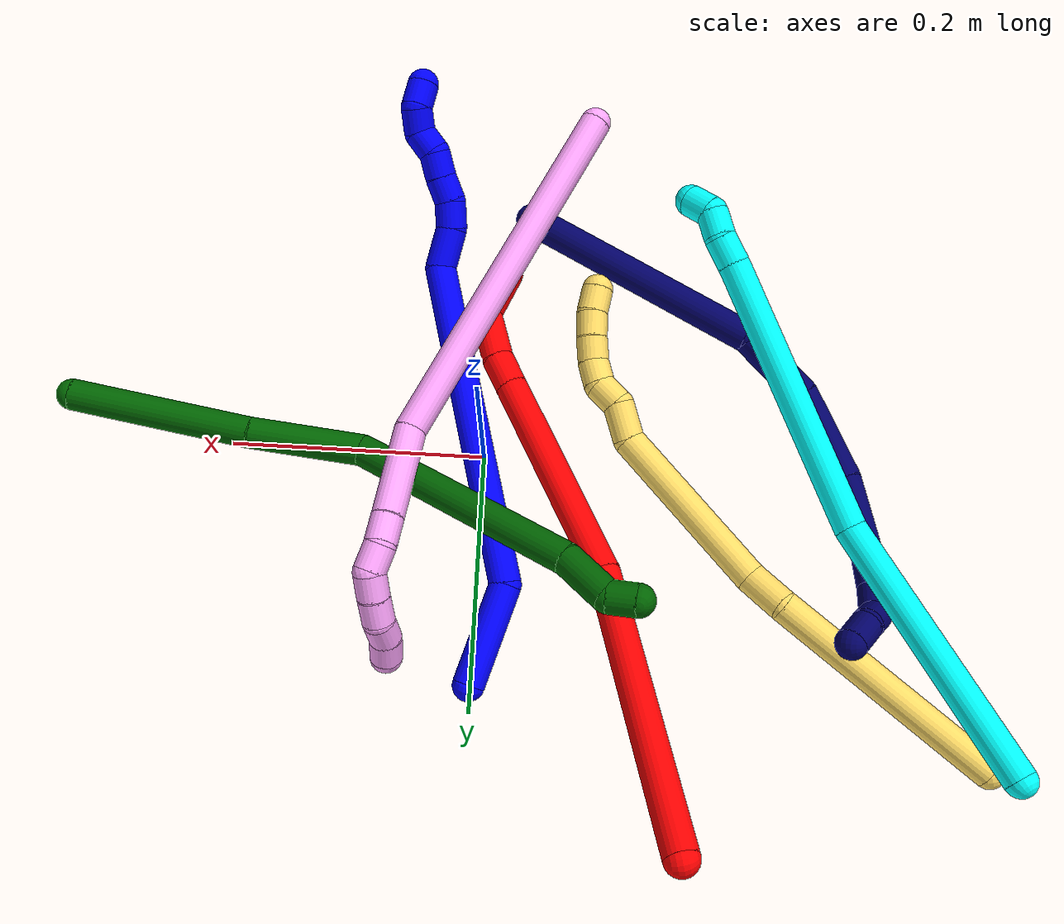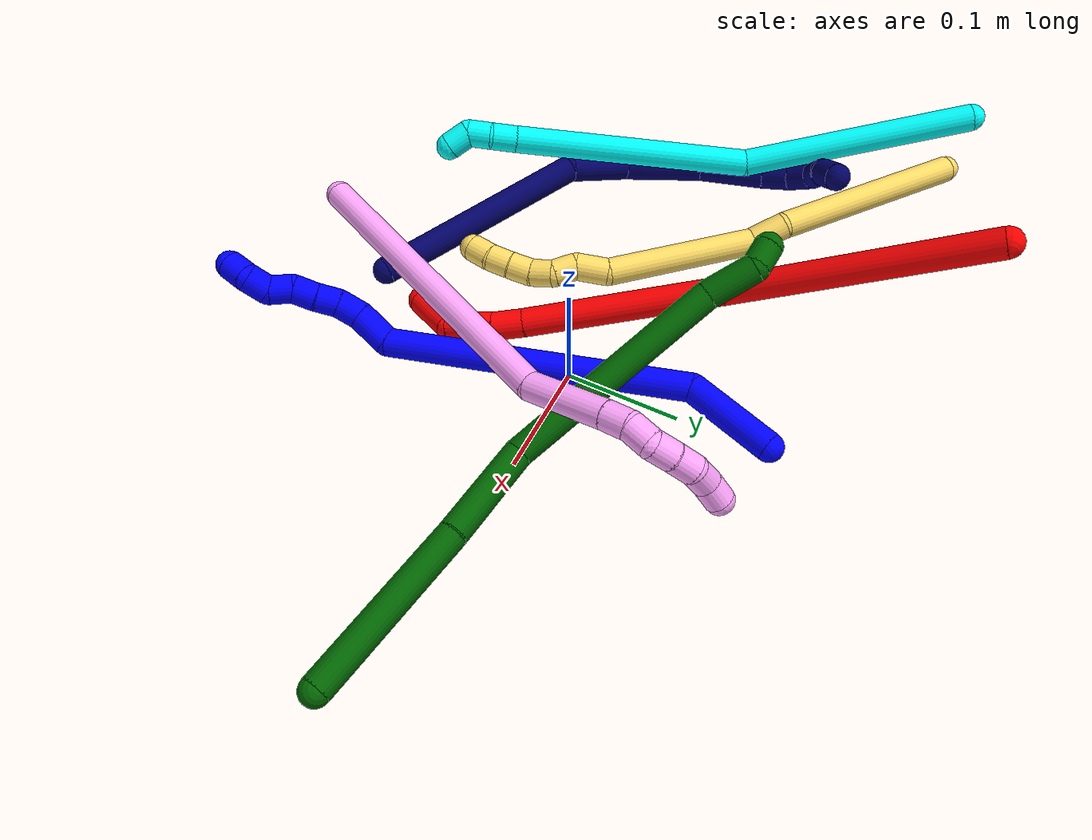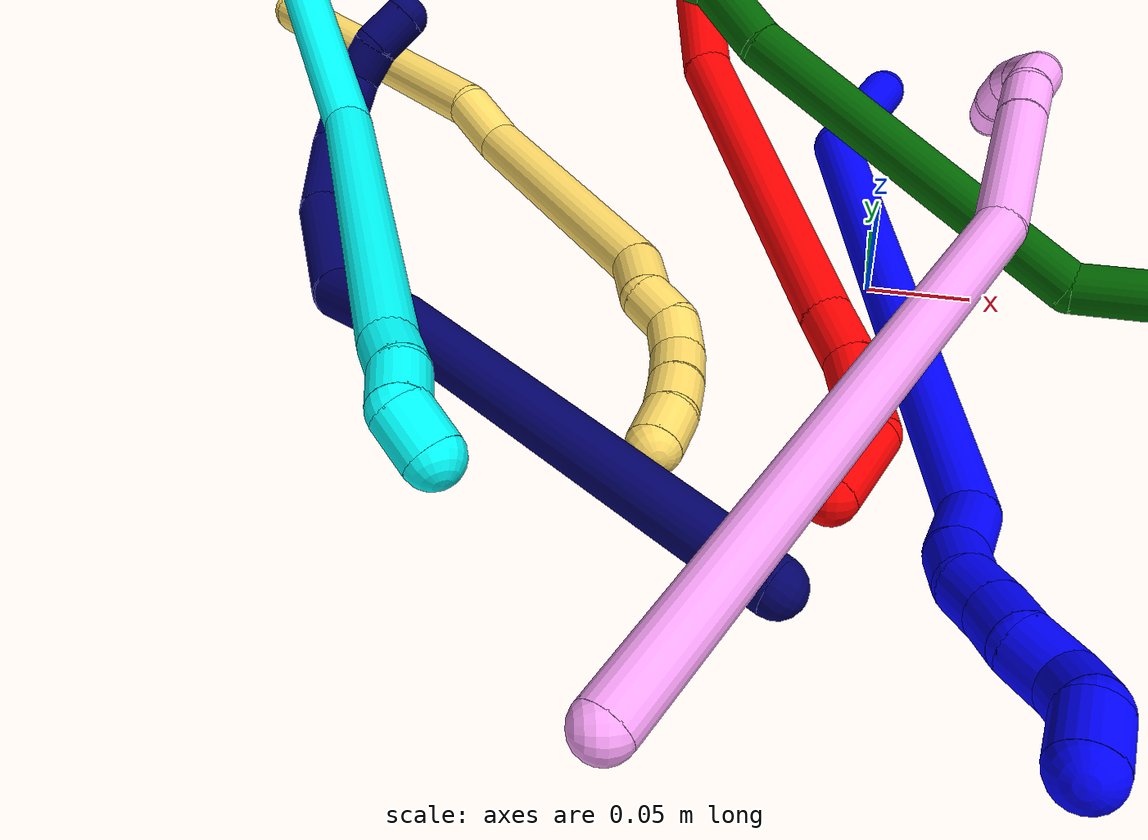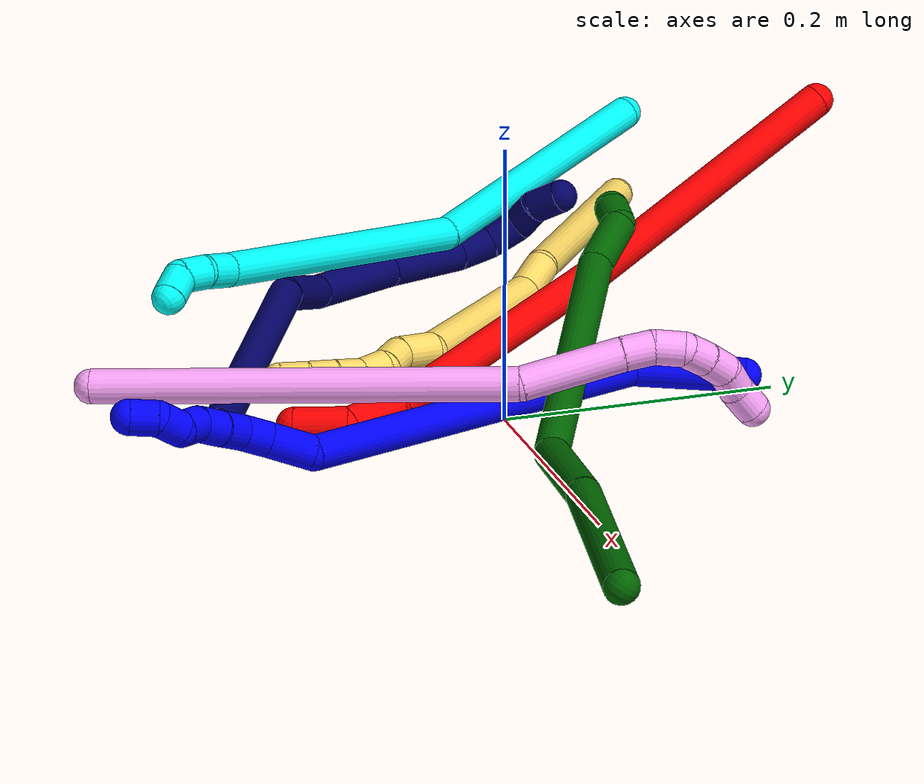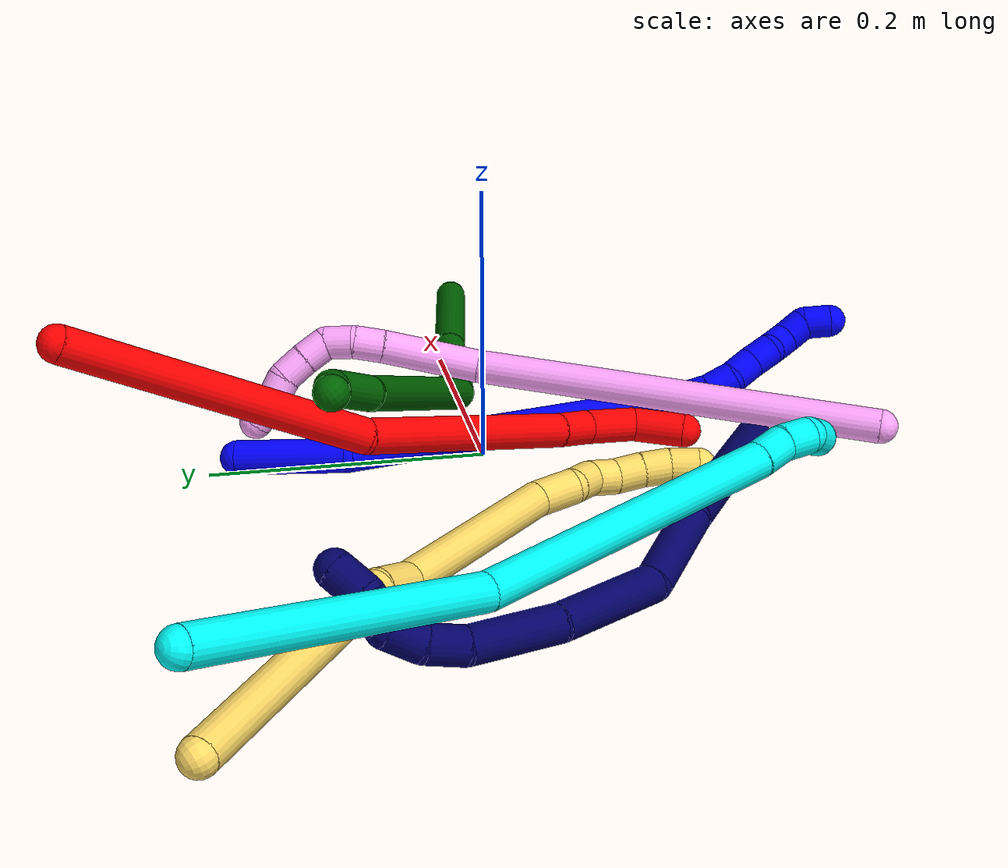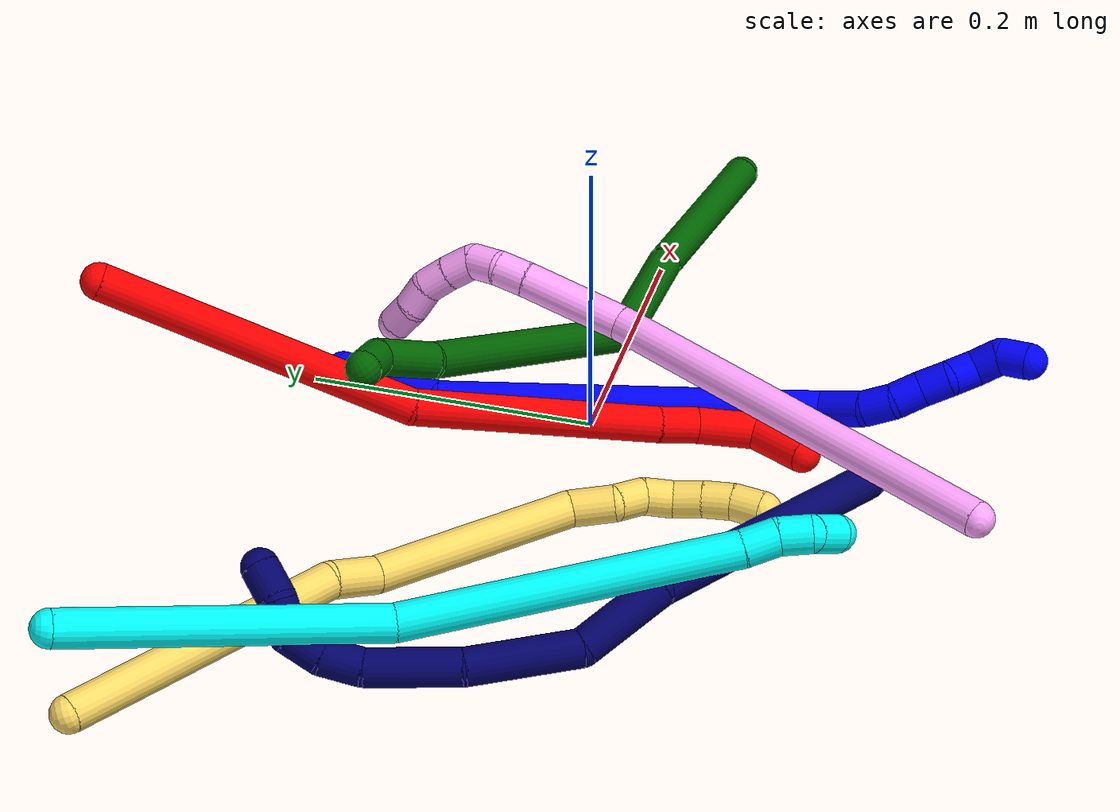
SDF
<sdf version="1.7">
 <world name="default">
  <plugin name="TubeGeneratorPlugin" filename="libtube_generator_plugin.so"/>
  <model name="photoneo_s_sensor">
   <static>1</static>
   <pose>0 0 2 1.57079 1.57079 3.14159</pose>
   <link name="link">
    <inertial><mass>0.1</mass></inertial>
    <sensor name="sensor" type="depth">
     <update_rate>30</update_rate>
     <camera>
      <horizontal_fov>1.22</horizontal_fov>
      <image><width>1920</width><height>1200</height><format>B8G8R8</format></image>
      <clip><near>0.1</near><far>4</far></clip>
      <depth_camera><output>points</output></depth_camera>
     </camera>
     <plugin name="camera_plugin" filename="libgazebo_ros_depth_camera.so">
      <baseline>0.2</baseline>
      <alwaysOn>1</alwaysOn>
      <updateRate>0.0</updateRate>
      <cameraName>camera_ir</cameraName>
      <imageTopicName>/camera/color/image_raw</imageTopicName>
      <cameraInfoTopicName>/camera/color/camera_info</cameraInfoTopicName>
      <depthImageTopicName>/camera/depth/image_raw</depthImageTopicName>
      <depthImageCameraInfoTopicName>/camera/depth/camera_info</depthImageCameraInfoTopicName>
      <pointCloudTopicName>/camera/depth/points</pointCloudTopicName>
      <frameName>fr_optical</frameName>
      <pointCloudCutoff>0.1</pointCloudCutoff>
      <pointCloudCutoffMax>2.0</pointCloudCutoffMax>
      <distortionK1>0</distortionK1>
      <distortionK2>0</distortionK2>
      <distortionK3>0</distortionK3>
      <distortionT1>0</distortionT1>
      <distortionT2>0</distortionT2>
      <CxPrime>0</CxPrime>
      <Cx>0</Cx>
      <Cy>0</Cy>
      <focalLength>0</focalLength>
      <hackBaseline>0</hackBaseline>
     </plugin>
    </sensor>
   </link>
  </model>
  <gravity>0 0 -9.8</gravity>
  <magnetic_field>6e-06 2.3e-05 -4.2e-05</magnetic_field>
  <atmosphere type="adiabatic"/>
  <physics name="default_physics" default="0" type="ode">
   <max_step_size>0.003</max_step_size>
   <real_time_factor>1</real_time_factor>
   <real_time_update_rate>1000</real_time_update_rate>
   <max_contacts>10000</max_contacts>
   <ode>
    <solver>
     <type>quick</type>
     <iters>100</iters>
     <sor>1.3</sor>
     <use_dynamic_moi_rescaling>0</use_dynamic_moi_rescaling>
    </solver>
    <constraints>
     <contact_max_correcting_vel>0</contact_max_correcting_vel>
     <contact_surface_layer>0.001</contact_surface_layer>
     <cfm>0</cfm>
     <erp>0.2</erp>
    </constraints>
   </ode>
  </physics>
  <scene><ambient>0.4 0.4 0.4 1</ambient><background>0.7 0.7 0.7 1</background><shadows>0</shadows></scene>
  <audio><device>default</device></audio>
  <spherical_coordinates>
   <surface_model>EARTH_WGS84</surface_model>
   <latitude_deg>0</latitude_deg>
   <longitude_deg>0</longitude_deg>
   <elevation>0</elevation>
   <heading_deg>0</heading_deg>
  </spherical_coordinates>
  <model name="bin">
   <static>1</static>
   <link name="bottom">
    <collision name="collision-bottom">
     <pose>0 0 -0.01 0 -0 0</pose>
     <geometry><box><size>0.8 0.6 0.02</size></box></geometry>
     <surface>
      <friction><ode><mu>100</mu><mu2>100</mu2></ode></friction>
      <contact><collide_bitmask>65535</collide_bitmask></contact>
     </surface>
    </collision>
   </link>
   <link name="west_wall">
    <collision name="collision-west_wall">
     <pose>-0.41 0 0.1 0 -0 0</pose>
     <geometry><box><size>0.02 0.6 0.2</size></box></geometry>
     <surface>
      <friction><ode><mu>100</mu><mu2>100</mu2></ode></friction>
      <contact><collide_bitmask>65535</collide_bitmask></contact>
     </surface>
    </collision>
   </link>
   <link name="east_wall">
    <collision name="collision-east_wall">
     <pose>0.41 0 0.1 0 -0 0</pose>
     <geometry><box><size>0.02 0.6 0.2</size></box></geometry>
     <surface>
      <friction><ode><mu>100</mu><mu2>100</mu2></ode></friction>
      <contact><collide_bitmask>65535</collide_bitmask></contact>
     </surface>
    </collision>
   </link>
   <link name="south_wall">
    <collision name="collision-south_wall">
     <pose>0 -0.31 0.1 0 -0 0</pose>
     <geometry><box><size>0.8 0.02 0.2</size></box></geometry>
     <surface>
      <friction><ode><mu>100</mu><mu2>100</mu2></ode></friction>
      <contact><collide_bitmask>65535</collide_bitmask></contact>
     </surface>
    </collision>
   </link>
   <link name="north_wall">
    <collision name="collision-north_wall">
     <pose>0 0.31 0.1 0 -0 0</pose>
     <geometry><box><size>0.8 0.02 0.2</size></box></geometry>
     <surface>
      <friction><ode><mu>100</mu><mu2>100</mu2></ode></friction>
      <contact><collide_bitmask>65535</collide_bitmask></contact>
     </surface>
    </collision>
   </link>
  </model>
  <model name="1">
   <static>0</static>
   <link name="1">
    <collision name="collision-cylinder-e_1_1_4">
     <pose>-0.011676 -0.016722 0.034514 0.451163 -0.295531 -0.068292</pose>
     <geometry><cylinder><radius>0.0125</radius><length>0.080178</length></cylinder></geometry>
     <surface>
      <friction><ode><mu>1.16</mu><mu2>1.16</mu2><slip1>0</slip1><slip2>0</slip2></ode></friction>
      <contact><ode><kp>1e+06</kp><kd>1</kd><max_vel>0</max_vel><min_depth>0.001</min_depth></ode></contact>
     </surface>
    </collision>
    <visual name="visual-cylinder-e_1_1_4">
     <pose>-0.011676 -0.016722 0.034514 0.451163 -0.295531 -0.068292</pose>
     <geometry><cylinder><radius>0.0125</radius><length>0.080178</length></cylinder></geometry>
     <material><ambient>0 0 1 1</ambient></material>
    </visual>
    <collision name="collision-cylinder-e_2_4_5">
     <pose>0.001085 -0.121821 0.164183 0.748489 0.185995 0.073229</pose>
     <geometry><cylinder><radius>0.0125</radius><length>0.26429</length></cylinder></geometry>
     <surface>
      <friction><ode><mu>1.16</mu><mu2>1.16</mu2><slip1>0</slip1><slip2>0</slip2></ode></friction>
      <contact><ode><kp>1e+06</kp><kd>1</kd><max_vel>0</max_vel><min_depth>0.001</min_depth></ode></contact>
     </surface>
    </collision>
    <visual name="visual-cylinder-e_2_4_5">
     <pose>0.001085 -0.121821 0.164183 0.748489 0.185995 0.073229</pose>
     <geometry><cylinder><radius>0.0125</radius><length>0.26429</length></cylinder></geometry>
     <material><ambient>0 0 1 1</ambient></material>
    </visual>
    <collision name="collision-cylinder-e_3_5_6">
     <pose>0.023386 -0.213946 0.275475 0.228146 -0.1282 -0.014708</pose>
     <geometry><cylinder><radius>0.0125</radius><length>0.033408</length></cylinder></geometry>
     <surface>
      <friction><ode><mu>1.16</mu><mu2>1.16</mu2><slip1>0</slip1><slip2>0</slip2></ode></friction>
      <contact><ode><kp>1e+06</kp><kd>1</kd><max_vel>0</max_vel><min_depth>0.001</min_depth></ode></contact>
     </surface>
    </collision>
    <visual name="visual-cylinder-e_3_5_6">
     <pose>0.023386 -0.213946 0.275475 0.228146 -0.1282 -0.014708</pose>
     <geometry><cylinder><radius>0.0125</radius><length>0.033408</length></cylinder></geometry>
     <material><ambient>0 0 1 1</ambient></material>
    </visual>
    <collision name="collision-cylinder-e_4_6_7">
     <pose>0.023343 -0.220634 0.301858 0.279517 0.193792 0.027346</pose>
     <geometry><cylinder><radius>0.0125</radius><length>0.021724</length></cylinder></geometry>
     <surface>
      <friction><ode><mu>1.16</mu><mu2>1.16</mu2><slip1>0</slip1><slip2>0</slip2></ode></friction>
      <contact><ode><kp>1e+06</kp><kd>1</kd><max_vel>0</max_vel><min_depth>0.001</min_depth></ode></contact>
     </surface>
    </collision>
    <visual name="visual-cylinder-e_4_6_7">
     <pose>0.023343 -0.220634 0.301858 0.279517 0.193792 0.027346</pose>
     <geometry><cylinder><radius>0.0125</radius><length>0.021724</length></cylinder></geometry>
     <material><ambient>0 0 1 1</ambient></material>
    </visual>
    <collision name="collision-cylinder-e_5_7_8">
     <pose>0.030269 -0.226941 0.320324 0.388608 0.498338 0.100064</pose>
     <geometry><cylinder><radius>0.0125</radius><length>0.020229</length></cylinder></geometry>
     <surface>
      <friction><ode><mu>1.16</mu><mu2>1.16</mu2><slip1>0</slip1><slip2>0</slip2></ode></friction>
      <contact><ode><kp>1e+06</kp><kd>1</kd><max_vel>0</max_vel><min_depth>0.001</min_depth></ode></contact>
     </surface>
    </collision>
    <visual name="visual-cylinder-e_5_7_8">
     <pose>0.030269 -0.226941 0.320324 0.388608 0.498338 0.100064</pose>
     <geometry><cylinder><radius>0.0125</radius><length>0.020229</length></cylinder></geometry>
     <material><ambient>0 0 1 1</ambient></material>
    </visual>
    <collision name="collision-cylinder-e_6_8_9">
     <pose>0.038884 -0.233422 0.337299 0.341865 0.386482 0.067531</pose>
     <geometry><cylinder><radius>0.0125</radius><length>0.020061</length></cylinder></geometry>
     <surface>
      <friction><ode><mu>1.16</mu><mu2>1.16</mu2><slip1>0</slip1><slip2>0</slip2></ode></friction>
      <contact><ode><kp>1e+06</kp><kd>1</kd><max_vel>0</max_vel><min_depth>0.001</min_depth></ode></contact>
     </surface>
    </collision>
    <visual name="visual-cylinder-e_6_8_9">
     <pose>0.038884 -0.233422 0.337299 0.341865 0.386482 0.067531</pose>
     <geometry><cylinder><radius>0.0125</radius><length>0.020061</length></cylinder></geometry>
     <material><ambient>0 0 1 1</ambient></material>
    </visual>
    <collision name="collision-cylinder-e_7_9_10">
     <pose>0.048754 -0.242032 0.351811 0.761997 0.652996 0.269634</pose>
     <geometry><cylinder><radius>0.0125</radius><length>0.020044</length></cylinder></geometry>
     <surface>
      <friction><ode><mu>1.16</mu><mu2>1.16</mu2><slip1>0</slip1><slip2>0</slip2></ode></friction>
      <contact><ode><kp>1e+06</kp><kd>1</kd><max_vel>0</max_vel><min_depth>0.001</min_depth></ode></contact>
     </surface>
    </collision>
    <visual name="visual-cylinder-e_7_9_10">
     <pose>0.048754 -0.242032 0.351811 0.761997 0.652996 0.269634</pose>
     <geometry><cylinder><radius>0.0125</radius><length>0.020044</length></cylinder></geometry>
     <material><ambient>0 0 1 1</ambient></material>
    </visual>
    <collision name="collision-cylinder-e_8_10_11">
     <pose>0.057897 -0.248797 0.36704 0.133351 0.309435 0.020828</pose>
     <geometry><cylinder><radius>0.0125</radius><length>0.020063</length></cylinder></geometry>
     <surface>
      <friction><ode><mu>1.16</mu><mu2>1.16</mu2><slip1>0</slip1><slip2>0</slip2></ode></friction>
      <contact><ode><kp>1e+06</kp><kd>1</kd><max_vel>0</max_vel><min_depth>0.001</min_depth></ode></contact>
     </surface>
    </collision>
    <visual name="visual-cylinder-e_8_10_11">
     <pose>0.057897 -0.248797 0.36704 0.133351 0.309435 0.020828</pose>
     <geometry><cylinder><radius>0.0125</radius><length>0.020063</length></cylinder></geometry>
     <material><ambient>0 0 1 1</ambient></material>
    </visual>
    <collision name="collision-cylinder-e_9_11_2">
     <pose>0.058992 -0.254464 0.385278 0.464806 -0.197311 -0.046843</pose>
     <geometry><cylinder><radius>0.0125</radius><length>0.020003</length></cylinder></geometry>
     <surface>
      <friction><ode><mu>1.16</mu><mu2>1.16</mu2><slip1>0</slip1><slip2>0</slip2></ode></friction>
      <contact><ode><kp>1e+06</kp><kd>1</kd><max_vel>0</max_vel><min_depth>0.001</min_depth></ode></contact>
     </surface>
    </collision>
    <visual name="visual-cylinder-e_9_11_2">
     <pose>0.058992 -0.254464 0.385278 0.464806 -0.197311 -0.046843</pose>
     <geometry><cylinder><radius>0.0125</radius><length>0.020003</length></cylinder></geometry>
     <material><ambient>0 0 1 1</ambient></material>
    </visual>
    <collision name="collision-sphere-2">
     <pose>0.057031 -0.25886 0.394045 0 -0 0</pose>
     <geometry><sphere><radius>0.0125</radius></sphere></geometry>
     <surface>
      <friction><ode><mu>1.16</mu><mu2>1.16</mu2><slip1>0</slip1><slip2>0</slip2></ode></friction>
      <contact><ode><kp>1e+06</kp><kd>1</kd><max_vel>0</max_vel><min_depth>0.001</min_depth></ode></contact>
     </surface>
    </collision>
    <visual name="visual-sphere-2">
     <pose>0.057031 -0.25886 0.394045 0 -0 0</pose>
     <geometry><sphere><radius>0.0125</radius></sphere></geometry>
     <material><ambient>0 0 1 1</ambient></material>
    </visual>
    <collision name="collision-sphere-11">
     <pose>0.060952 -0.250068 0.376511 0 -0 0</pose>
     <geometry><sphere><radius>0.0125</radius></sphere></geometry>
     <surface>
      <friction><ode><mu>1.16</mu><mu2>1.16</mu2><slip1>0</slip1><slip2>0</slip2></ode></friction>
      <contact><ode><kp>1e+06</kp><kd>1</kd><max_vel>0</max_vel><min_depth>0.001</min_depth></ode></contact>
     </surface>
    </collision>
    <visual name="visual-sphere-11">
     <pose>0.060952 -0.250068 0.376511 0 -0 0</pose>
     <geometry><sphere><radius>0.0125</radius></sphere></geometry>
     <material><ambient>0 0 1 1</ambient></material>
    </visual>
    <collision name="collision-sphere-10">
     <pose>0.054843 -0.247527 0.35757 0 -0 0</pose>
     <geometry><sphere><radius>0.0125</radius></sphere></geometry>
     <surface>
      <friction><ode><mu>1.16</mu><mu2>1.16</mu2><slip1>0</slip1><slip2>0</slip2></ode></friction>
      <contact><ode><kp>1e+06</kp><kd>1</kd><max_vel>0</max_vel><min_depth>0.001</min_depth></ode></contact>
     </surface>
    </collision>
    <visual name="visual-sphere-10">
     <pose>0.054843 -0.247527 0.35757 0 -0 0</pose>
     <geometry><sphere><radius>0.0125</radius></sphere></geometry>
     <material><ambient>0 0 1 1</ambient></material>
    </visual>
    <collision name="collision-sphere-9">
     <pose>0.042665 -0.236536 0.346052 0 -0 0</pose>
     <geometry><sphere><radius>0.0125</radius></sphere></geometry>
     <surface>
      <friction><ode><mu>1.16</mu><mu2>1.16</mu2><slip1>0</slip1><slip2>0</slip2></ode></friction>
      <contact><ode><kp>1e+06</kp><kd>1</kd><max_vel>0</max_vel><min_depth>0.001</min_depth></ode></contact>
     </surface>
    </collision>
    <visual name="visual-sphere-9">
     <pose>0.042665 -0.236536 0.346052 0 -0 0</pose>
     <geometry><sphere><radius>0.0125</radius></sphere></geometry>
     <material><ambient>0 0 1 1</ambient></material>
    </visual>
    <collision name="collision-sphere-4">
     <pose>-0.023352 -0.033443 0.069028 0 -0 0</pose>
     <geometry><sphere><radius>0.0125</radius></sphere></geometry>
     <surface>
      <friction><ode><mu>1.16</mu><mu2>1.16</mu2><slip1>0</slip1><slip2>0</slip2></ode></friction>
      <contact><ode><kp>1e+06</kp><kd>1</kd><max_vel>0</max_vel><min_depth>0.001</min_depth></ode></contact>
     </surface>
    </collision>
    <visual name="visual-sphere-4">
     <pose>-0.023352 -0.033443 0.069028 0 -0 0</pose>
     <geometry><sphere><radius>0.0125</radius></sphere></geometry>
     <material><ambient>0 0 1 1</ambient></material>
    </visual>
    <collision name="collision-sphere-1">
     <geometry><sphere><radius>0.0125</radius></sphere></geometry>
     <surface>
      <friction><ode><mu>1.16</mu><mu2>1.16</mu2><slip1>0</slip1><slip2>0</slip2></ode></friction>
      <contact><ode><kp>1e+06</kp><kd>1</kd><max_vel>0</max_vel><min_depth>0.001</min_depth></ode></contact>
     </surface>
    </collision>
    <visual name="visual-sphere-1">
     <geometry><sphere><radius>0.0125</radius></sphere></geometry>
     <material><ambient>0 0 1 1</ambient></material>
    </visual>
    <collision name="collision-sphere-8">
     <pose>0.035103 -0.230307 0.328546 0 -0 0</pose>
     <geometry><sphere><radius>0.0125</radius></sphere></geometry>
     <surface>
      <friction><ode><mu>1.16</mu><mu2>1.16</mu2><slip1>0</slip1><slip2>0</slip2></ode></friction>
      <contact><ode><kp>1e+06</kp><kd>1</kd><max_vel>0</max_vel><min_depth>0.001</min_depth></ode></contact>
     </surface>
    </collision>
    <visual name="visual-sphere-8">
     <pose>0.035103 -0.230307 0.328546 0 -0 0</pose>
     <geometry><sphere><radius>0.0125</radius></sphere></geometry>
     <material><ambient>0 0 1 1</ambient></material>
    </visual>
    <collision name="collision-sphere-5">
     <pose>0.025522 -0.210199 0.259338 0 -0 0</pose>
     <geometry><sphere><radius>0.0125</radius></sphere></geometry>
     <surface>
      <friction><ode><mu>1.16</mu><mu2>1.16</mu2><slip1>0</slip1><slip2>0</slip2></ode></friction>
      <contact><ode><kp>1e+06</kp><kd>1</kd><max_vel>0</max_vel><min_depth>0.001</min_depth></ode></contact>
     </surface>
    </collision>
    <visual name="visual-sphere-5">
     <pose>0.025522 -0.210199 0.259338 0 -0 0</pose>
     <geometry><sphere><radius>0.0125</radius></sphere></geometry>
     <material><ambient>0 0 1 1</ambient></material>
    </visual>
    <collision name="collision-sphere-6">
     <pose>0.021251 -0.217693 0.291613 0 -0 0</pose>
     <geometry><sphere><radius>0.0125</radius></sphere></geometry>
     <surface>
      <friction><ode><mu>1.16</mu><mu2>1.16</mu2><slip1>0</slip1><slip2>0</slip2></ode></friction>
      <contact><ode><kp>1e+06</kp><kd>1</kd><max_vel>0</max_vel><min_depth>0.001</min_depth></ode></contact>
     </surface>
    </collision>
    <visual name="visual-sphere-6">
     <pose>0.021251 -0.217693 0.291613 0 -0 0</pose>
     <geometry><sphere><radius>0.0125</radius></sphere></geometry>
     <material><ambient>0 0 1 1</ambient></material>
    </visual>
    <collision name="collision-sphere-7">
     <pose>0.025434 -0.223574 0.312103 0 -0 0</pose>
     <geometry><sphere><radius>0.0125</radius></sphere></geometry>
     <surface>
      <friction><ode><mu>1.16</mu><mu2>1.16</mu2><slip1>0</slip1><slip2>0</slip2></ode></friction>
      <contact><ode><kp>1e+06</kp><kd>1</kd><max_vel>0</max_vel><min_depth>0.001</min_depth></ode></contact>
     </surface>
    </collision>
    <visual name="visual-sphere-7">
     <pose>0.025434 -0.223574 0.312103 0 -0 0</pose>
     <geometry><sphere><radius>0.0125</radius></sphere></geometry>
     <material><ambient>0 0 1 1</ambient></material>
    </visual>
    <inertial>
     <pose>0.0107 -0.139367 0.194577 0 -0 0</pose>
     <mass>0.5</mass>
     <inertia>
      <ixx>0.001688</ixx>
      <ixy>0</ixy>
      <ixz>0</ixz>
      <iyy>0.001289</iyy>
      <iyz>0</iyz>
      <izz>0.000815</izz>
     </inertia>
    </inertial>
   </link>
   <pose>0.001053 0.179313 0.012117 0.921515 -0.372205 0.048371</pose>
  </model>
  <model name="2">
   <static>0</static>
   <link name="2">
    <collision name="collision-cylinder-e_1_1_4">
     <pose>0.046627 -0.100273 0.003404 1.53686 0.435041 0.420956</pose>
     <geometry><cylinder><radius>0.0125</radius><length>0.221272</length></cylinder></geometry>
     <surface>
      <friction><ode><mu>1.16</mu><mu2>1.16</mu2><slip1>0</slip1><slip2>0</slip2></ode></friction>
      <contact><ode><kp>1e+06</kp><kd>1</kd><max_vel>0</max_vel><min_depth>0.001</min_depth></ode></contact>
     </surface>
    </collision>
    <visual name="visual-cylinder-e_1_1_4">
     <pose>0.046627 -0.100273 0.003404 1.53686 0.435041 0.420956</pose>
     <geometry><cylinder><radius>0.0125</radius><length>0.221272</length></cylinder></geometry>
     <material><ambient>1 0 0 1</ambient></material>
    </visual>
    <collision name="collision-cylinder-e_2_4_5">
     <pose>0.109907 -0.282431 0.026214 1.33809 0.195356 0.154652</pose>
     <geometry><cylinder><radius>0.0125</radius><length>0.17157</length></cylinder></geometry>
     <surface>
      <friction><ode><mu>1.16</mu><mu2>1.16</mu2><slip1>0</slip1><slip2>0</slip2></ode></friction>
      <contact><ode><kp>1e+06</kp><kd>1</kd><max_vel>0</max_vel><min_depth>0.001</min_depth></ode></contact>
     </surface>
    </collision>
    <visual name="visual-cylinder-e_2_4_5">
     <pose>0.109907 -0.282431 0.026214 1.33809 0.195356 0.154652</pose>
     <geometry><cylinder><radius>0.0125</radius><length>0.17157</length></cylinder></geometry>
     <material><ambient>1 0 0 1</ambient></material>
    </visual>
    <collision name="collision-cylinder-e_3_5_6">
     <pose>0.128367 -0.377422 0.048732 1.33774 0.133399 0.105499</pose>
     <geometry><cylinder><radius>0.0125</radius><length>0.027182</length></cylinder></geometry>
     <surface>
      <friction><ode><mu>1.16</mu><mu2>1.16</mu2><slip1>0</slip1><slip2>0</slip2></ode></friction>
      <contact><ode><kp>1e+06</kp><kd>1</kd><max_vel>0</max_vel><min_depth>0.001</min_depth></ode></contact>
     </surface>
    </collision>
    <visual name="visual-cylinder-e_3_5_6">
     <pose>0.128367 -0.377422 0.048732 1.33774 0.133399 0.105499</pose>
     <geometry><cylinder><radius>0.0125</radius><length>0.027182</length></cylinder></geometry>
     <material><ambient>1 0 0 1</ambient></material>
    </visual>
    <collision name="collision-cylinder-e_4_6_7">
     <pose>0.13248 -0.410943 0.052908 1.51871 0.11231 0.106619</pose>
     <geometry><cylinder><radius>0.0125</radius><length>0.041145</length></cylinder></geometry>
     <surface>
      <friction><ode><mu>1.16</mu><mu2>1.16</mu2><slip1>0</slip1><slip2>0</slip2></ode></friction>
      <contact><ode><kp>1e+06</kp><kd>1</kd><max_vel>0</max_vel><min_depth>0.001</min_depth></ode></contact>
     </surface>
    </collision>
    <visual name="visual-cylinder-e_4_6_7">
     <pose>0.13248 -0.410943 0.052908 1.51871 0.11231 0.106619</pose>
     <geometry><cylinder><radius>0.0125</radius><length>0.041145</length></cylinder></geometry>
     <material><ambient>1 0 0 1</ambient></material>
    </visual>
    <collision name="collision-cylinder-e_5_7_2">
     <pose>0.13598 -0.446714 0.042151 2.22688 0.061527 0.12489</pose>
     <geometry><cylinder><radius>0.0125</radius><length>0.03883</length></cylinder></geometry>
     <surface>
      <friction><ode><mu>1.16</mu><mu2>1.16</mu2><slip1>0</slip1><slip2>0</slip2></ode></friction>
      <contact><ode><kp>1e+06</kp><kd>1</kd><max_vel>0</max_vel><min_depth>0.001</min_depth></ode></contact>
     </surface>
    </collision>
    <visual name="visual-cylinder-e_5_7_2">
     <pose>0.13598 -0.446714 0.042151 2.22688 0.061527 0.12489</pose>
     <geometry><cylinder><radius>0.0125</radius><length>0.03883</length></cylinder></geometry>
     <material><ambient>1 0 0 1</ambient></material>
    </visual>
    <collision name="collision-sphere-2">
     <pose>0.137173 -0.462069 0.03033 0 -0 0</pose>
     <geometry><sphere><radius>0.0125</radius></sphere></geometry>
     <surface>
      <friction><ode><mu>1.16</mu><mu2>1.16</mu2><slip1>0</slip1><slip2>0</slip2></ode></friction>
      <contact><ode><kp>1e+06</kp><kd>1</kd><max_vel>0</max_vel><min_depth>0.001</min_depth></ode></contact>
     </surface>
    </collision>
    <visual name="visual-sphere-2">
     <pose>0.137173 -0.462069 0.03033 0 -0 0</pose>
     <geometry><sphere><radius>0.0125</radius></sphere></geometry>
     <material><ambient>1 0 0 1</ambient></material>
    </visual>
    <collision name="collision-sphere-7">
     <pose>0.134786 -0.431359 0.053972 0 -0 0</pose>
     <geometry><sphere><radius>0.0125</radius></sphere></geometry>
     <surface>
      <friction><ode><mu>1.16</mu><mu2>1.16</mu2><slip1>0</slip1><slip2>0</slip2></ode></friction>
      <contact><ode><kp>1e+06</kp><kd>1</kd><max_vel>0</max_vel><min_depth>0.001</min_depth></ode></contact>
     </surface>
    </collision>
    <visual name="visual-sphere-7">
     <pose>0.134786 -0.431359 0.053972 0 -0 0</pose>
     <geometry><sphere><radius>0.0125</radius></sphere></geometry>
     <material><ambient>1 0 0 1</ambient></material>
    </visual>
    <collision name="collision-sphere-6">
     <pose>0.130174 -0.390528 0.051843 0 -0 0</pose>
     <geometry><sphere><radius>0.0125</radius></sphere></geometry>
     <surface>
      <friction><ode><mu>1.16</mu><mu2>1.16</mu2><slip1>0</slip1><slip2>0</slip2></ode></friction>
      <contact><ode><kp>1e+06</kp><kd>1</kd><max_vel>0</max_vel><min_depth>0.001</min_depth></ode></contact>
     </surface>
    </collision>
    <visual name="visual-sphere-6">
     <pose>0.130174 -0.390528 0.051843 0 -0 0</pose>
     <geometry><sphere><radius>0.0125</radius></sphere></geometry>
     <material><ambient>1 0 0 1</ambient></material>
    </visual>
    <collision name="collision-sphere-5">
     <pose>0.126559 -0.364316 0.045621 0 -0 0</pose>
     <geometry><sphere><radius>0.0125</radius></sphere></geometry>
     <surface>
      <friction><ode><mu>1.16</mu><mu2>1.16</mu2><slip1>0</slip1><slip2>0</slip2></ode></friction>
      <contact><ode><kp>1e+06</kp><kd>1</kd><max_vel>0</max_vel><min_depth>0.001</min_depth></ode></contact>
     </surface>
    </collision>
    <visual name="visual-sphere-5">
     <pose>0.126559 -0.364316 0.045621 0 -0 0</pose>
     <geometry><sphere><radius>0.0125</radius></sphere></geometry>
     <material><ambient>1 0 0 1</ambient></material>
    </visual>
    <collision name="collision-sphere-1">
     <geometry><sphere><radius>0.0125</radius></sphere></geometry>
     <surface>
      <friction><ode><mu>1.16</mu><mu2>1.16</mu2><slip1>0</slip1><slip2>0</slip2></ode></friction>
      <contact><ode><kp>1e+06</kp><kd>1</kd><max_vel>0</max_vel><min_depth>0.001</min_depth></ode></contact>
     </surface>
    </collision>
    <visual name="visual-sphere-1">
     <geometry><sphere><radius>0.0125</radius></sphere></geometry>
     <material><ambient>1 0 0 1</ambient></material>
    </visual>
    <collision name="collision-sphere-4">
     <pose>0.093255 -0.200546 0.006807 0 -0 0</pose>
     <geometry><sphere><radius>0.0125</radius></sphere></geometry>
     <surface>
      <friction><ode><mu>1.16</mu><mu2>1.16</mu2><slip1>0</slip1><slip2>0</slip2></ode></friction>
      <contact><ode><kp>1e+06</kp><kd>1</kd><max_vel>0</max_vel><min_depth>0.001</min_depth></ode></contact>
     </surface>
    </collision>
    <visual name="visual-sphere-4">
     <pose>0.093255 -0.200546 0.006807 0 -0 0</pose>
     <geometry><sphere><radius>0.0125</radius></sphere></geometry>
     <material><ambient>1 0 0 1</ambient></material>
    </visual>
    <inertial>
     <pose>0.086789 -0.230316 0.020778 0 -0 0</pose>
     <mass>0.5</mass>
     <inertia><ixx>0.0016</ixx><ixy>0</ixy><ixz>0</ixz><iyy>0.00066</iyy><iyz>0</iyz><izz>0.000783</izz></inertia>
    </inertial>
   </link>
   <pose>-0.14523 0.288503 0.159843 2.80413 1.50773 3.05539</pose>
  </model>
  <model name="3">
   <static>0</static>
   <link name="3">
    <collision name="collision-cylinder-e_1_1_4">
     <pose>0.009735 -0.00715 -0.105658 3.07402 0.091673 1.87157</pose>
     <geometry><cylinder><radius>0.0125</radius><length>0.212692</length></cylinder></geometry>
     <surface>
      <friction><ode><mu>1.16</mu><mu2>1.16</mu2><slip1>0</slip1><slip2>0</slip2></ode></friction>
      <contact><ode><kp>1e+06</kp><kd>1</kd><max_vel>0</max_vel><min_depth>0.001</min_depth></ode></contact>
     </surface>
    </collision>
    <visual name="visual-cylinder-e_1_1_4">
     <pose>0.009735 -0.00715 -0.105658 3.07402 0.091673 1.87157</pose>
     <geometry><cylinder><radius>0.0125</radius><length>0.212692</length></cylinder></geometry>
     <material><ambient>0.003922 1 0.996078 1</ambient></material>
    </visual>
    <collision name="collision-cylinder-e_2_4_5">
     <pose>0.055931 -0.044878 -0.310788 2.84336 0.336995 1.69474</pose>
     <geometry><cylinder><radius>0.0125</radius><length>0.220536</length></cylinder></geometry>
     <surface>
      <friction><ode><mu>1.16</mu><mu2>1.16</mu2><slip1>0</slip1><slip2>0</slip2></ode></friction>
      <contact><ode><kp>1e+06</kp><kd>1</kd><max_vel>0</max_vel><min_depth>0.001</min_depth></ode></contact>
     </surface>
    </collision>
    <visual name="visual-cylinder-e_2_4_5">
     <pose>0.055931 -0.044878 -0.310788 2.84336 0.336995 1.69474</pose>
     <geometry><cylinder><radius>0.0125</radius><length>0.220536</length></cylinder></geometry>
     <material><ambient>0.003922 1 0.996078 1</ambient></material>
    </visual>
    <collision name="collision-cylinder-e_3_5_6">
     <pose>0.097614 -0.078215 -0.420375 2.87527 0.462124 2.10638</pose>
     <geometry><cylinder><radius>0.0125</radius><length>0.023427</length></cylinder></geometry>
     <surface>
      <friction><ode><mu>1.16</mu><mu2>1.16</mu2><slip1>0</slip1><slip2>0</slip2></ode></friction>
      <contact><ode><kp>1e+06</kp><kd>1</kd><max_vel>0</max_vel><min_depth>0.001</min_depth></ode></contact>
     </surface>
    </collision>
    <visual name="visual-cylinder-e_3_5_6">
     <pose>0.097614 -0.078215 -0.420375 2.87527 0.462124 2.10638</pose>
     <geometry><cylinder><radius>0.0125</radius><length>0.023427</length></cylinder></geometry>
     <material><ambient>0.003922 1 0.996078 1</ambient></material>
    </visual>
    <collision name="collision-cylinder-e_4_6_7">
     <pose>0.105092 -0.084821 -0.440186 2.76392 0.212939 1.0198</pose>
     <geometry><cylinder><radius>0.0125</radius><length>0.021343</length></cylinder></geometry>
     <surface>
      <friction><ode><mu>1.16</mu><mu2>1.16</mu2><slip1>0</slip1><slip2>0</slip2></ode></friction>
      <contact><ode><kp>1e+06</kp><kd>1</kd><max_vel>0</max_vel><min_depth>0.001</min_depth></ode></contact>
     </surface>
    </collision>
    <visual name="visual-cylinder-e_4_6_7">
     <pose>0.105092 -0.084821 -0.440186 2.76392 0.212939 1.0198</pose>
     <geometry><cylinder><radius>0.0125</radius><length>0.021343</length></cylinder></geometry>
     <material><ambient>0.003922 1 0.996078 1</ambient></material>
    </visual>
    <collision name="collision-cylinder-e_5_7_2">
     <pose>0.107461 -0.085228 -0.46033 -2.82356 0.01039 -0.064764</pose>
     <geometry><cylinder><radius>0.0125</radius><length>0.022001</length></cylinder></geometry>
     <surface>
      <friction><ode><mu>1.16</mu><mu2>1.16</mu2><slip1>0</slip1><slip2>0</slip2></ode></friction>
      <contact><ode><kp>1e+06</kp><kd>1</kd><max_vel>0</max_vel><min_depth>0.001</min_depth></ode></contact>
     </surface>
    </collision>
    <visual name="visual-cylinder-e_5_7_2">
     <pose>0.107461 -0.085228 -0.46033 -2.82356 0.01039 -0.064764</pose>
     <geometry><cylinder><radius>0.0125</radius><length>0.022001</length></cylinder></geometry>
     <material><ambient>0.003922 1 0.996078 1</ambient></material>
    </visual>
    <collision name="collision-sphere-2">
     <pose>0.107576 -0.081788 -0.470778 0 -0 0</pose>
     <geometry><sphere><radius>0.0125</radius></sphere></geometry>
     <surface>
      <friction><ode><mu>1.16</mu><mu2>1.16</mu2><slip1>0</slip1><slip2>0</slip2></ode></friction>
      <contact><ode><kp>1e+06</kp><kd>1</kd><max_vel>0</max_vel><min_depth>0.001</min_depth></ode></contact>
     </surface>
    </collision>
    <visual name="visual-sphere-2">
     <pose>0.107576 -0.081788 -0.470778 0 -0 0</pose>
     <geometry><sphere><radius>0.0125</radius></sphere></geometry>
     <material><ambient>0.003922 1 0.996078 1</ambient></material>
    </visual>
    <collision name="collision-sphere-7">
     <pose>0.107347 -0.088667 -0.449882 0 -0 0</pose>
     <geometry><sphere><radius>0.0125</radius></sphere></geometry>
     <surface>
      <friction><ode><mu>1.16</mu><mu2>1.16</mu2><slip1>0</slip1><slip2>0</slip2></ode></friction>
      <contact><ode><kp>1e+06</kp><kd>1</kd><max_vel>0</max_vel><min_depth>0.001</min_depth></ode></contact>
     </surface>
    </collision>
    <visual name="visual-sphere-7">
     <pose>0.107347 -0.088667 -0.449882 0 -0 0</pose>
     <geometry><sphere><radius>0.0125</radius></sphere></geometry>
     <material><ambient>0.003922 1 0.996078 1</ambient></material>
    </visual>
    <collision name="collision-sphere-6">
     <pose>0.102837 -0.080975 -0.430491 0 -0 0</pose>
     <geometry><sphere><radius>0.0125</radius></sphere></geometry>
     <surface>
      <friction><ode><mu>1.16</mu><mu2>1.16</mu2><slip1>0</slip1><slip2>0</slip2></ode></friction>
      <contact><ode><kp>1e+06</kp><kd>1</kd><max_vel>0</max_vel><min_depth>0.001</min_depth></ode></contact>
     </surface>
    </collision>
    <visual name="visual-sphere-6">
     <pose>0.102837 -0.080975 -0.430491 0 -0 0</pose>
     <geometry><sphere><radius>0.0125</radius></sphere></geometry>
     <material><ambient>0.003922 1 0.996078 1</ambient></material>
    </visual>
    <collision name="collision-sphere-5">
     <pose>0.092392 -0.075456 -0.41026 0 -0 0</pose>
     <geometry><sphere><radius>0.0125</radius></sphere></geometry>
     <surface>
      <friction><ode><mu>1.16</mu><mu2>1.16</mu2><slip1>0</slip1><slip2>0</slip2></ode></friction>
      <contact><ode><kp>1e+06</kp><kd>1</kd><max_vel>0</max_vel><min_depth>0.001</min_depth></ode></contact>
     </surface>
    </collision>
    <visual name="visual-sphere-5">
     <pose>0.092392 -0.075456 -0.41026 0 -0 0</pose>
     <geometry><sphere><radius>0.0125</radius></sphere></geometry>
     <material><ambient>0.003922 1 0.996078 1</ambient></material>
    </visual>
    <collision name="collision-sphere-1">
     <geometry><sphere><radius>0.0125</radius></sphere></geometry>
     <surface>
      <friction><ode><mu>1.16</mu><mu2>1.16</mu2><slip1>0</slip1><slip2>0</slip2></ode></friction>
      <contact><ode><kp>1e+06</kp><kd>1</kd><max_vel>0</max_vel><min_depth>0.001</min_depth></ode></contact>
     </surface>
    </collision>
    <visual name="visual-sphere-1">
     <geometry><sphere><radius>0.0125</radius></sphere></geometry>
     <material><ambient>0.003922 1 0.996078 1</ambient></material>
    </visual>
    <collision name="collision-sphere-4">
     <pose>0.019471 -0.0143 -0.211316 0 -0 0</pose>
     <geometry><sphere><radius>0.0125</radius></sphere></geometry>
     <surface>
      <friction><ode><mu>1.16</mu><mu2>1.16</mu2><slip1>0</slip1><slip2>0</slip2></ode></friction>
      <contact><ode><kp>1e+06</kp><kd>1</kd><max_vel>0</max_vel><min_depth>0.001</min_depth></ode></contact>
     </surface>
    </collision>
    <visual name="visual-sphere-4">
     <pose>0.019471 -0.0143 -0.211316 0 -0 0</pose>
     <geometry><sphere><radius>0.0125</radius></sphere></geometry>
     <material><ambient>0.003922 1 0.996078 1</ambient></material>
    </visual>
    <inertial>
     <pose>0.042599 -0.033871 -0.240767 0 -0 0</pose>
     <mass>0.5</mass>
     <inertia>
      <ixx>0.001284</ixx>
      <ixy>0</ixy>
      <ixz>0</ixz>
      <iyy>0.002049</iyy>
      <iyz>0</iyz>
      <izz>-0.000105</izz>
     </inertia>
    </inertial>
   </link>
   <pose>-0.387814 0.227929 0.078773 -0.929898 -1.03583 -0.009928</pose>
  </model>
  <model name="4">
   <static>0</static>
   <link name="4">
    <collision name="collision-cylinder-e_1_1_4">
     <pose>0.105404 -0.035809 -0.101976 2.80389 0.772863 2.34809</pose>
     <geometry><cylinder><radius>0.0125</radius><length>0.301937</length></cylinder></geometry>
     <surface>
      <friction><ode><mu>1.16</mu><mu2>1.16</mu2><slip1>0</slip1><slip2>0</slip2></ode></friction>
      <contact><ode><kp>1e+06</kp><kd>1</kd><max_vel>0</max_vel><min_depth>0.001</min_depth></ode></contact>
     </surface>
    </collision>
    <visual name="visual-cylinder-e_1_1_4">
     <pose>0.105404 -0.035809 -0.101976 2.80389 0.772863 2.34809</pose>
     <geometry><cylinder><radius>0.0125</radius><length>0.301937</length></cylinder></geometry>
     <material><ambient>1 0.65098 0.996078 1</ambient></material>
    </visual>
    <collision name="collision-cylinder-e_2_4_5">
     <pose>0.241167 -0.086448 -0.218449 2.34486 0.971504 1.79554</pose>
     <geometry><cylinder><radius>0.0125</radius><length>0.07353</length></cylinder></geometry>
     <surface>
      <friction><ode><mu>1.16</mu><mu2>1.16</mu2><slip1>0</slip1><slip2>0</slip2></ode></friction>
      <contact><ode><kp>1e+06</kp><kd>1</kd><max_vel>0</max_vel><min_depth>0.001</min_depth></ode></contact>
     </surface>
    </collision>
    <visual name="visual-cylinder-e_2_4_5">
     <pose>0.241167 -0.086448 -0.218449 2.34486 0.971504 1.79554</pose>
     <geometry><cylinder><radius>0.0125</radius><length>0.07353</length></cylinder></geometry>
     <material><ambient>1 0.65098 0.996078 1</ambient></material>
    </visual>
    <collision name="collision-cylinder-e_3_5_6">
     <pose>0.280809 -0.105098 -0.237593 2.45345 0.995764 1.97592</pose>
     <geometry><cylinder><radius>0.0125</radius><length>0.022126</length></cylinder></geometry>
     <surface>
      <friction><ode><mu>1.16</mu><mu2>1.16</mu2><slip1>0</slip1><slip2>0</slip2></ode></friction>
      <contact><ode><kp>1e+06</kp><kd>1</kd><max_vel>0</max_vel><min_depth>0.001</min_depth></ode></contact>
     </surface>
    </collision>
    <visual name="visual-cylinder-e_3_5_6">
     <pose>0.280809 -0.105098 -0.237593 2.45345 0.995764 1.97592</pose>
     <geometry><cylinder><radius>0.0125</radius><length>0.022126</length></cylinder></geometry>
     <material><ambient>1 0.65098 0.996078 1</ambient></material>
    </visual>
    <collision name="collision-cylinder-e_4_6_7">
     <pose>0.298618 -0.10996 -0.248492 2.97675 0.931485 2.81579</pose>
     <geometry><cylinder><radius>0.0125</radius><length>0.021244</length></cylinder></geometry>
     <surface>
      <friction><ode><mu>1.16</mu><mu2>1.16</mu2><slip1>0</slip1><slip2>0</slip2></ode></friction>
      <contact><ode><kp>1e+06</kp><kd>1</kd><max_vel>0</max_vel><min_depth>0.001</min_depth></ode></contact>
     </surface>
    </collision>
    <visual name="visual-cylinder-e_4_6_7">
     <pose>0.298618 -0.10996 -0.248492 2.97675 0.931485 2.81579</pose>
     <geometry><cylinder><radius>0.0125</radius><length>0.021244</length></cylinder></geometry>
     <material><ambient>1 0.65098 0.996078 1</ambient></material>
    </visual>
    <collision name="collision-cylinder-e_5_7_8">
     <pose>0.316376 -0.107133 -0.256314 -1.95657 1.14629 -1.52866</pose>
     <geometry><cylinder><radius>0.0125</radius><length>0.020266</length></cylinder></geometry>
     <surface>
      <friction><ode><mu>1.16</mu><mu2>1.16</mu2><slip1>0</slip1><slip2>0</slip2></ode></friction>
      <contact><ode><kp>1e+06</kp><kd>1</kd><max_vel>0</max_vel><min_depth>0.001</min_depth></ode></contact>
     </surface>
    </collision>
    <visual name="visual-cylinder-e_5_7_8">
     <pose>0.316376 -0.107133 -0.256314 -1.95657 1.14629 -1.52866</pose>
     <geometry><cylinder><radius>0.0125</radius><length>0.020266</length></cylinder></geometry>
     <material><ambient>1 0.65098 0.996078 1</ambient></material>
    </visual>
    <collision name="collision-cylinder-e_6_8_9">
     <pose>0.334509 -0.098631 -0.259185 -1.84426 1.07497 -1.33253</pose>
     <geometry><cylinder><radius>0.0125</radius><length>0.020237</length></cylinder></geometry>
     <surface>
      <friction><ode><mu>1.16</mu><mu2>1.16</mu2><slip1>0</slip1><slip2>0</slip2></ode></friction>
      <contact><ode><kp>1e+06</kp><kd>1</kd><max_vel>0</max_vel><min_depth>0.001</min_depth></ode></contact>
     </surface>
    </collision>
    <visual name="visual-cylinder-e_6_8_9">
     <pose>0.334509 -0.098631 -0.259185 -1.84426 1.07497 -1.33253</pose>
     <geometry><cylinder><radius>0.0125</radius><length>0.020237</length></cylinder></geometry>
     <material><ambient>1 0.65098 0.996078 1</ambient></material>
    </visual>
    <collision name="collision-cylinder-e_7_9_10">
     <pose>0.35011 -0.086427 -0.26102 -1.64138 0.723381 -0.77138</pose>
     <geometry><cylinder><radius>0.0125</radius><length>0.020246</length></cylinder></geometry>
     <surface>
      <friction><ode><mu>1.16</mu><mu2>1.16</mu2><slip1>0</slip1><slip2>0</slip2></ode></friction>
      <contact><ode><kp>1e+06</kp><kd>1</kd><max_vel>0</max_vel><min_depth>0.001</min_depth></ode></contact>
     </surface>
    </collision>
    <visual name="visual-cylinder-e_7_9_10">
     <pose>0.35011 -0.086427 -0.26102 -1.64138 0.723381 -0.77138</pose>
     <geometry><cylinder><radius>0.0125</radius><length>0.020246</length></cylinder></geometry>
     <material><ambient>1 0.65098 0.996078 1</ambient></material>
    </visual>
    <collision name="collision-cylinder-e_8_10_2">
     <pose>0.363859 -0.072044 -0.264393 -1.96541 0.762322 -1.08234</pose>
     <geometry><cylinder><radius>0.0125</radius><length>0.020413</length></cylinder></geometry>
     <surface>
      <friction><ode><mu>1.16</mu><mu2>1.16</mu2><slip1>0</slip1><slip2>0</slip2></ode></friction>
      <contact><ode><kp>1e+06</kp><kd>1</kd><max_vel>0</max_vel><min_depth>0.001</min_depth></ode></contact>
     </surface>
    </collision>
    <visual name="visual-cylinder-e_8_10_2">
     <pose>0.363859 -0.072044 -0.264393 -1.96541 0.762322 -1.08234</pose>
     <geometry><cylinder><radius>0.0125</radius><length>0.020413</length></cylinder></geometry>
     <material><ambient>1 0.65098 0.996078 1</ambient></material>
    </visual>
    <collision name="collision-sphere-2">
     <pose>0.370908 -0.065229 -0.267231 0 -0 0</pose>
     <geometry><sphere><radius>0.0125</radius></sphere></geometry>
     <surface>
      <friction><ode><mu>1.16</mu><mu2>1.16</mu2><slip1>0</slip1><slip2>0</slip2></ode></friction>
      <contact><ode><kp>1e+06</kp><kd>1</kd><max_vel>0</max_vel><min_depth>0.001</min_depth></ode></contact>
     </surface>
    </collision>
    <visual name="visual-sphere-2">
     <pose>0.370908 -0.065229 -0.267231 0 -0 0</pose>
     <geometry><sphere><radius>0.0125</radius></sphere></geometry>
     <material><ambient>1 0.65098 0.996078 1</ambient></material>
    </visual>
    <collision name="collision-sphere-10">
     <pose>0.35681 -0.078858 -0.261555 0 -0 0</pose>
     <geometry><sphere><radius>0.0125</radius></sphere></geometry>
     <surface>
      <friction><ode><mu>1.16</mu><mu2>1.16</mu2><slip1>0</slip1><slip2>0</slip2></ode></friction>
      <contact><ode><kp>1e+06</kp><kd>1</kd><max_vel>0</max_vel><min_depth>0.001</min_depth></ode></contact>
     </surface>
    </collision>
    <visual name="visual-sphere-10">
     <pose>0.35681 -0.078858 -0.261555 0 -0 0</pose>
     <geometry><sphere><radius>0.0125</radius></sphere></geometry>
     <material><ambient>1 0.65098 0.996078 1</ambient></material>
    </visual>
    <collision name="collision-sphere-9">
     <pose>0.343409 -0.093996 -0.260485 0 -0 0</pose>
     <geometry><sphere><radius>0.0125</radius></sphere></geometry>
     <surface>
      <friction><ode><mu>1.16</mu><mu2>1.16</mu2><slip1>0</slip1><slip2>0</slip2></ode></friction>
      <contact><ode><kp>1e+06</kp><kd>1</kd><max_vel>0</max_vel><min_depth>0.001</min_depth></ode></contact>
     </surface>
    </collision>
    <visual name="visual-sphere-9">
     <pose>0.343409 -0.093996 -0.260485 0 -0 0</pose>
     <geometry><sphere><radius>0.0125</radius></sphere></geometry>
     <material><ambient>1 0.65098 0.996078 1</ambient></material>
    </visual>
    <collision name="collision-sphere-4">
     <pose>0.210809 -0.071619 -0.203952 0 -0 0</pose>
     <geometry><sphere><radius>0.0125</radius></sphere></geometry>
     <surface>
      <friction><ode><mu>1.16</mu><mu2>1.16</mu2><slip1>0</slip1><slip2>0</slip2></ode></friction>
      <contact><ode><kp>1e+06</kp><kd>1</kd><max_vel>0</max_vel><min_depth>0.001</min_depth></ode></contact>
     </surface>
    </collision>
    <visual name="visual-sphere-4">
     <pose>0.210809 -0.071619 -0.203952 0 -0 0</pose>
     <geometry><sphere><radius>0.0125</radius></sphere></geometry>
     <material><ambient>1 0.65098 0.996078 1</ambient></material>
    </visual>
    <collision name="collision-sphere-1">
     <geometry><sphere><radius>0.0125</radius></sphere></geometry>
     <surface>
      <friction><ode><mu>1.16</mu><mu2>1.16</mu2><slip1>0</slip1><slip2>0</slip2></ode></friction>
      <contact><ode><kp>1e+06</kp><kd>1</kd><max_vel>0</max_vel><min_depth>0.001</min_depth></ode></contact>
     </surface>
    </collision>
    <visual name="visual-sphere-1">
     <geometry><sphere><radius>0.0125</radius></sphere></geometry>
     <material><ambient>1 0.65098 0.996078 1</ambient></material>
    </visual>
    <collision name="collision-sphere-8">
     <pose>0.325609 -0.103266 -0.257885 0 -0 0</pose>
     <geometry><sphere><radius>0.0125</radius></sphere></geometry>
     <surface>
      <friction><ode><mu>1.16</mu><mu2>1.16</mu2><slip1>0</slip1><slip2>0</slip2></ode></friction>
      <contact><ode><kp>1e+06</kp><kd>1</kd><max_vel>0</max_vel><min_depth>0.001</min_depth></ode></contact>
     </surface>
    </collision>
    <visual name="visual-sphere-8">
     <pose>0.325609 -0.103266 -0.257885 0 -0 0</pose>
     <geometry><sphere><radius>0.0125</radius></sphere></geometry>
     <material><ambient>1 0.65098 0.996078 1</ambient></material>
    </visual>
    <collision name="collision-sphere-5">
     <pose>0.271526 -0.101277 -0.232945 0 -0 0</pose>
     <geometry><sphere><radius>0.0125</radius></sphere></geometry>
     <surface>
      <friction><ode><mu>1.16</mu><mu2>1.16</mu2><slip1>0</slip1><slip2>0</slip2></ode></friction>
      <contact><ode><kp>1e+06</kp><kd>1</kd><max_vel>0</max_vel><min_depth>0.001</min_depth></ode></contact>
     </surface>
    </collision>
    <visual name="visual-sphere-5">
     <pose>0.271526 -0.101277 -0.232945 0 -0 0</pose>
     <geometry><sphere><radius>0.0125</radius></sphere></geometry>
     <material><ambient>1 0.65098 0.996078 1</ambient></material>
    </visual>
    <collision name="collision-sphere-6">
     <pose>0.290093 -0.10892 -0.24224 0 -0 0</pose>
     <geometry><sphere><radius>0.0125</radius></sphere></geometry>
     <surface>
      <friction><ode><mu>1.16</mu><mu2>1.16</mu2><slip1>0</slip1><slip2>0</slip2></ode></friction>
      <contact><ode><kp>1e+06</kp><kd>1</kd><max_vel>0</max_vel><min_depth>0.001</min_depth></ode></contact>
     </surface>
    </collision>
    <visual name="visual-sphere-6">
     <pose>0.290093 -0.10892 -0.24224 0 -0 0</pose>
     <geometry><sphere><radius>0.0125</radius></sphere></geometry>
     <material><ambient>1 0.65098 0.996078 1</ambient></material>
    </visual>
    <collision name="collision-sphere-7">
     <pose>0.307142 -0.111 -0.254744 0 -0 0</pose>
     <geometry><sphere><radius>0.0125</radius></sphere></geometry>
     <surface>
      <friction><ode><mu>1.16</mu><mu2>1.16</mu2><slip1>0</slip1><slip2>0</slip2></ode></friction>
      <contact><ode><kp>1e+06</kp><kd>1</kd><max_vel>0</max_vel><min_depth>0.001</min_depth></ode></contact>
     </surface>
    </collision>
    <visual name="visual-sphere-7">
     <pose>0.307142 -0.111 -0.254744 0 -0 0</pose>
     <geometry><sphere><radius>0.0125</radius></sphere></geometry>
     <material><ambient>1 0.65098 0.996078 1</ambient></material>
    </visual>
    <inertial>
     <pose>0.179625 -0.058436 -0.157021 0 -0 0</pose>
     <mass>0.5</mass>
     <inertia>
      <ixx>6.2e-05</ixx>
      <ixy>0</ixy>
      <ixz>0</ixz>
      <iyy>0.003128</iyy>
      <iyz>0</iyz>
      <izz>-0.001109</izz>
     </inertia>
    </inertial>
   </link>
   <pose>-0.074737 -0.278346 0.031505 -1.4518 0.140025 1.89799</pose>
  </model>
  <model name="5">
   <static>0</static>
   <link name="5">
    <collision name="collision-cylinder-e_1_1_4">
     <pose>0.02658 -0.051167 -0.07696 2.55485 0.280052 0.873109</pose>
     <geometry><cylinder><radius>0.0125</radius><length>0.192328</length></cylinder></geometry>
     <surface>
      <friction><ode><mu>1.16</mu><mu2>1.16</mu2><slip1>0</slip1><slip2>0</slip2></ode></friction>
      <contact><ode><kp>1e+06</kp><kd>1</kd><max_vel>0</max_vel><min_depth>0.001</min_depth></ode></contact>
     </surface>
    </collision>
    <visual name="visual-cylinder-e_1_1_4">
     <pose>0.02658 -0.051167 -0.07696 2.55485 0.280052 0.873109</pose>
     <geometry><cylinder><radius>0.0125</radius><length>0.192328</length></cylinder></geometry>
     <material><ambient>1 0.858824 0.4 1</ambient></material>
    </visual>
    <collision name="collision-cylinder-e_2_4_5">
     <pose>0.062942 -0.108884 -0.165875 2.6404 0.622458 1.79731</pose>
     <geometry><cylinder><radius>0.0125</radius><length>0.033555</length></cylinder></geometry>
     <surface>
      <friction><ode><mu>1.16</mu><mu2>1.16</mu2><slip1>0</slip1><slip2>0</slip2></ode></friction>
      <contact><ode><kp>1e+06</kp><kd>1</kd><max_vel>0</max_vel><min_depth>0.001</min_depth></ode></contact>
     </surface>
    </collision>
    <visual name="visual-cylinder-e_2_4_5">
     <pose>0.062942 -0.108884 -0.165875 2.6404 0.622458 1.79731</pose>
     <geometry><cylinder><radius>0.0125</radius><length>0.033555</length></cylinder></geometry>
     <material><ambient>1 0.858824 0.4 1</ambient></material>
    </visual>
    <collision name="collision-cylinder-e_3_5_6">
     <pose>0.094794 -0.141894 -0.239453 2.736 0.317918 1.3244</pose>
     <geometry><cylinder><radius>0.0125</radius><length>0.141206</length></cylinder></geometry>
     <surface>
      <friction><ode><mu>1.16</mu><mu2>1.16</mu2><slip1>0</slip1><slip2>0</slip2></ode></friction>
      <contact><ode><kp>1e+06</kp><kd>1</kd><max_vel>0</max_vel><min_depth>0.001</min_depth></ode></contact>
     </surface>
    </collision>
    <visual name="visual-cylinder-e_3_5_6">
     <pose>0.094794 -0.141894 -0.239453 2.736 0.317918 1.3244</pose>
     <geometry><cylinder><radius>0.0125</radius><length>0.141206</length></cylinder></geometry>
     <material><ambient>1 0.858824 0.4 1</ambient></material>
    </visual>
    <collision name="collision-cylinder-e_4_6_7">
     <pose>0.120053 -0.167788 -0.31557 -3.10241 0.216423 -2.78468</pose>
     <geometry><cylinder><radius>0.0125</radius><length>0.029701</length></cylinder></geometry>
     <surface>
      <friction><ode><mu>1.16</mu><mu2>1.16</mu2><slip1>0</slip1><slip2>0</slip2></ode></friction>
      <contact><ode><kp>1e+06</kp><kd>1</kd><max_vel>0</max_vel><min_depth>0.001</min_depth></ode></contact>
     </surface>
    </collision>
    <visual name="visual-cylinder-e_4_6_7">
     <pose>0.120053 -0.167788 -0.31557 -3.10241 0.216423 -2.78468</pose>
     <geometry><cylinder><radius>0.0125</radius><length>0.029701</length></cylinder></geometry>
     <material><ambient>1 0.858824 0.4 1</ambient></material>
    </visual>
    <collision name="collision-cylinder-e_5_7_8">
     <pose>0.127778 -0.171438 -0.338865 2.69459 0.435082 1.54286</pose>
     <geometry><cylinder><radius>0.0125</radius><length>0.021527</length></cylinder></geometry>
     <surface>
      <friction><ode><mu>1.16</mu><mu2>1.16</mu2><slip1>0</slip1><slip2>0</slip2></ode></friction>
      <contact><ode><kp>1e+06</kp><kd>1</kd><max_vel>0</max_vel><min_depth>0.001</min_depth></ode></contact>
     </surface>
    </collision>
    <visual name="visual-cylinder-e_5_7_8">
     <pose>0.127778 -0.171438 -0.338865 2.69459 0.435082 1.54286</pose>
     <geometry><cylinder><radius>0.0125</radius><length>0.021527</length></cylinder></geometry>
     <material><ambient>1 0.858824 0.4 1</ambient></material>
    </visual>
    <collision name="collision-cylinder-e_6_8_9">
     <pose>0.136812 -0.174553 -0.356733 -3.02033 0.457567 -2.63155</pose>
     <geometry><cylinder><radius>0.0125</radius><length>0.020361</length></cylinder></geometry>
     <surface>
      <friction><ode><mu>1.16</mu><mu2>1.16</mu2><slip1>0</slip1><slip2>0</slip2></ode></friction>
      <contact><ode><kp>1e+06</kp><kd>1</kd><max_vel>0</max_vel><min_depth>0.001</min_depth></ode></contact>
     </surface>
    </collision>
    <visual name="visual-cylinder-e_6_8_9">
     <pose>0.136812 -0.174553 -0.356733 -3.02033 0.457567 -2.63155</pose>
     <geometry><cylinder><radius>0.0125</radius><length>0.020361</length></cylinder></geometry>
     <material><ambient>1 0.858824 0.4 1</ambient></material>
    </visual>
    <collision name="collision-cylinder-e_7_9_10">
     <pose>0.143106 -0.170996 -0.375599 -2.89646 0.175983 -1.24299</pose>
     <geometry><cylinder><radius>0.0125</radius><length>0.020521</length></cylinder></geometry>
     <surface>
      <friction><ode><mu>1.16</mu><mu2>1.16</mu2><slip1>0</slip1><slip2>0</slip2></ode></friction>
      <contact><ode><kp>1e+06</kp><kd>1</kd><max_vel>0</max_vel><min_depth>0.001</min_depth></ode></contact>
     </surface>
    </collision>
    <visual name="visual-cylinder-e_7_9_10">
     <pose>0.143106 -0.170996 -0.375599 -2.89646 0.175983 -1.24299</pose>
     <geometry><cylinder><radius>0.0125</radius><length>0.020521</length></cylinder></geometry>
     <material><ambient>1 0.858824 0.4 1</ambient></material>
    </visual>
    <collision name="collision-cylinder-e_8_10_11">
     <pose>0.147043 -0.165234 -0.39473 -2.80069 0.212952 -1.11137</pose>
     <geometry><cylinder><radius>0.0125</radius><length>0.02026</length></cylinder></geometry>
     <surface>
      <friction><ode><mu>1.16</mu><mu2>1.16</mu2><slip1>0</slip1><slip2>0</slip2></ode></friction>
      <contact><ode><kp>1e+06</kp><kd>1</kd><max_vel>0</max_vel><min_depth>0.001</min_depth></ode></contact>
     </surface>
    </collision>
    <visual name="visual-cylinder-e_8_10_11">
     <pose>0.147043 -0.165234 -0.39473 -2.80069 0.212952 -1.11137</pose>
     <geometry><cylinder><radius>0.0125</radius><length>0.02026</length></cylinder></geometry>
     <material><ambient>1 0.858824 0.4 1</ambient></material>
    </visual>
    <collision name="collision-cylinder-e_9_11_2">
     <pose>0.151536 -0.156603 -0.412526 -2.58034 0.231029 -0.765422</pose>
     <geometry><cylinder><radius>0.0125</radius><length>0.020541</length></cylinder></geometry>
     <surface>
      <friction><ode><mu>1.16</mu><mu2>1.16</mu2><slip1>0</slip1><slip2>0</slip2></ode></friction>
      <contact><ode><kp>1e+06</kp><kd>1</kd><max_vel>0</max_vel><min_depth>0.001</min_depth></ode></contact>
     </surface>
    </collision>
    <visual name="visual-cylinder-e_9_11_2">
     <pose>0.151536 -0.156603 -0.412526 -2.58034 0.231029 -0.765422</pose>
     <geometry><cylinder><radius>0.0125</radius><length>0.020541</length></cylinder></geometry>
     <material><ambient>1 0.858824 0.4 1</ambient></material>
    </visual>
    <collision name="collision-sphere-2">
     <pose>0.153888 -0.151282 -0.42099 0 -0 0</pose>
     <geometry><sphere><radius>0.0125</radius></sphere></geometry>
     <surface>
      <friction><ode><mu>1.16</mu><mu2>1.16</mu2><slip1>0</slip1><slip2>0</slip2></ode></friction>
      <contact><ode><kp>1e+06</kp><kd>1</kd><max_vel>0</max_vel><min_depth>0.001</min_depth></ode></contact>
     </surface>
    </collision>
    <visual name="visual-sphere-2">
     <pose>0.153888 -0.151282 -0.42099 0 -0 0</pose>
     <geometry><sphere><radius>0.0125</radius></sphere></geometry>
     <material><ambient>1 0.858824 0.4 1</ambient></material>
    </visual>
    <collision name="collision-sphere-11">
     <pose>0.149184 -0.161924 -0.404062 0 -0 0</pose>
     <geometry><sphere><radius>0.0125</radius></sphere></geometry>
     <surface>
      <friction><ode><mu>1.16</mu><mu2>1.16</mu2><slip1>0</slip1><slip2>0</slip2></ode></friction>
      <contact><ode><kp>1e+06</kp><kd>1</kd><max_vel>0</max_vel><min_depth>0.001</min_depth></ode></contact>
     </surface>
    </collision>
    <visual name="visual-sphere-11">
     <pose>0.149184 -0.161924 -0.404062 0 -0 0</pose>
     <geometry><sphere><radius>0.0125</radius></sphere></geometry>
     <material><ambient>1 0.858824 0.4 1</ambient></material>
    </visual>
    <collision name="collision-sphere-10">
     <pose>0.144902 -0.168545 -0.385399 0 -0 0</pose>
     <geometry><sphere><radius>0.0125</radius></sphere></geometry>
     <surface>
      <friction><ode><mu>1.16</mu><mu2>1.16</mu2><slip1>0</slip1><slip2>0</slip2></ode></friction>
      <contact><ode><kp>1e+06</kp><kd>1</kd><max_vel>0</max_vel><min_depth>0.001</min_depth></ode></contact>
     </surface>
    </collision>
    <visual name="visual-sphere-10">
     <pose>0.144902 -0.168545 -0.385399 0 -0 0</pose>
     <geometry><sphere><radius>0.0125</radius></sphere></geometry>
     <material><ambient>1 0.858824 0.4 1</ambient></material>
    </visual>
    <collision name="collision-sphere-9">
     <pose>0.14131 -0.173448 -0.365799 0 -0 0</pose>
     <geometry><sphere><radius>0.0125</radius></sphere></geometry>
     <surface>
      <friction><ode><mu>1.16</mu><mu2>1.16</mu2><slip1>0</slip1><slip2>0</slip2></ode></friction>
      <contact><ode><kp>1e+06</kp><kd>1</kd><max_vel>0</max_vel><min_depth>0.001</min_depth></ode></contact>
     </surface>
    </collision>
    <visual name="visual-sphere-9">
     <pose>0.14131 -0.173448 -0.365799 0 -0 0</pose>
     <geometry><sphere><radius>0.0125</radius></sphere></geometry>
     <material><ambient>1 0.858824 0.4 1</ambient></material>
    </visual>
    <collision name="collision-sphere-4">
     <pose>0.05316 -0.102335 -0.153921 0 -0 0</pose>
     <geometry><sphere><radius>0.0125</radius></sphere></geometry>
     <surface>
      <friction><ode><mu>1.16</mu><mu2>1.16</mu2><slip1>0</slip1><slip2>0</slip2></ode></friction>
      <contact><ode><kp>1e+06</kp><kd>1</kd><max_vel>0</max_vel><min_depth>0.001</min_depth></ode></contact>
     </surface>
    </collision>
    <visual name="visual-sphere-4">
     <pose>0.05316 -0.102335 -0.153921 0 -0 0</pose>
     <geometry><sphere><radius>0.0125</radius></sphere></geometry>
     <material><ambient>1 0.858824 0.4 1</ambient></material>
    </visual>
    <collision name="collision-sphere-1">
     <geometry><sphere><radius>0.0125</radius></sphere></geometry>
     <surface>
      <friction><ode><mu>1.16</mu><mu2>1.16</mu2><slip1>0</slip1><slip2>0</slip2></ode></friction>
      <contact><ode><kp>1e+06</kp><kd>1</kd><max_vel>0</max_vel><min_depth>0.001</min_depth></ode></contact>
     </surface>
    </collision>
    <visual name="visual-sphere-1">
     <geometry><sphere><radius>0.0125</radius></sphere></geometry>
     <material><ambient>1 0.858824 0.4 1</ambient></material>
    </visual>
    <collision name="collision-sphere-8">
     <pose>0.132315 -0.175658 -0.347666 0 -0 0</pose>
     <geometry><sphere><radius>0.0125</radius></sphere></geometry>
     <surface>
      <friction><ode><mu>1.16</mu><mu2>1.16</mu2><slip1>0</slip1><slip2>0</slip2></ode></friction>
      <contact><ode><kp>1e+06</kp><kd>1</kd><max_vel>0</max_vel><min_depth>0.001</min_depth></ode></contact>
     </surface>
    </collision>
    <visual name="visual-sphere-8">
     <pose>0.132315 -0.175658 -0.347666 0 -0 0</pose>
     <geometry><sphere><radius>0.0125</radius></sphere></geometry>
     <material><ambient>1 0.858824 0.4 1</ambient></material>
    </visual>
    <collision name="collision-sphere-5">
     <pose>0.072724 -0.115433 -0.17783 0 -0 0</pose>
     <geometry><sphere><radius>0.0125</radius></sphere></geometry>
     <surface>
      <friction><ode><mu>1.16</mu><mu2>1.16</mu2><slip1>0</slip1><slip2>0</slip2></ode></friction>
      <contact><ode><kp>1e+06</kp><kd>1</kd><max_vel>0</max_vel><min_depth>0.001</min_depth></ode></contact>
     </surface>
    </collision>
    <visual name="visual-sphere-5">
     <pose>0.072724 -0.115433 -0.17783 0 -0 0</pose>
     <geometry><sphere><radius>0.0125</radius></sphere></geometry>
     <material><ambient>1 0.858824 0.4 1</ambient></material>
    </visual>
    <collision name="collision-sphere-6">
     <pose>0.116864 -0.168356 -0.301077 0 -0 0</pose>
     <geometry><sphere><radius>0.0125</radius></sphere></geometry>
     <surface>
      <friction><ode><mu>1.16</mu><mu2>1.16</mu2><slip1>0</slip1><slip2>0</slip2></ode></friction>
      <contact><ode><kp>1e+06</kp><kd>1</kd><max_vel>0</max_vel><min_depth>0.001</min_depth></ode></contact>
     </surface>
    </collision>
    <visual name="visual-sphere-6">
     <pose>0.116864 -0.168356 -0.301077 0 -0 0</pose>
     <geometry><sphere><radius>0.0125</radius></sphere></geometry>
     <material><ambient>1 0.858824 0.4 1</ambient></material>
    </visual>
    <collision name="collision-sphere-7">
     <pose>0.123242 -0.167219 -0.330063 0 -0 0</pose>
     <geometry><sphere><radius>0.0125</radius></sphere></geometry>
     <surface>
      <friction><ode><mu>1.16</mu><mu2>1.16</mu2><slip1>0</slip1><slip2>0</slip2></ode></friction>
      <contact><ode><kp>1e+06</kp><kd>1</kd><max_vel>0</max_vel><min_depth>0.001</min_depth></ode></contact>
     </surface>
    </collision>
    <visual name="visual-sphere-7">
     <pose>0.123242 -0.167219 -0.330063 0 -0 0</pose>
     <geometry><sphere><radius>0.0125</radius></sphere></geometry>
     <material><ambient>1 0.858824 0.4 1</ambient></material>
    </visual>
    <inertial>
     <pose>0.07748 -0.111665 -0.204579 0 -0 0</pose>
     <mass>0.5</mass>
     <inertia><ixx>0.001098</ixx><ixy>0</ixy><ixz>0</ixz><iyy>0.00038</iyy><iyz>0</iyz><izz>0.00013</izz></inertia>
    </inertial>
   </link>
   <pose>-0.387904 0.221993 0.013027 -2.88113 1.23164 -0.950197</pose>
  </model>
  <model name="6">
   <static>0</static>
   <link name="6">
    <collision name="collision-cylinder-e_1_1_4">
     <pose>-0.070676 0.018493 0.004961 -1.30869 -1.30624 1.0615</pose>
     <geometry><cylinder><radius>0.0125</radius><length>0.146447</length></cylinder></geometry>
     <surface>
      <friction><ode><mu>1.16</mu><mu2>1.16</mu2><slip1>0</slip1><slip2>0</slip2></ode></friction>
      <contact><ode><kp>1e+06</kp><kd>1</kd><max_vel>0</max_vel><min_depth>0.001</min_depth></ode></contact>
     </surface>
    </collision>
    <visual name="visual-cylinder-e_1_1_4">
     <pose>-0.070676 0.018493 0.004961 -1.30869 -1.30624 1.0615</pose>
     <geometry><cylinder><radius>0.0125</radius><length>0.146447</length></cylinder></geometry>
     <material><ambient>0 0.392157 0.003922 1</ambient></material>
    </visual>
    <collision name="collision-cylinder-e_2_4_5">
     <pose>-0.184726 0.047511 0.007552 -1.7923 -1.32701 1.5479</pose>
     <geometry><cylinder><radius>0.0125</radius><length>0.089392</length></cylinder></geometry>
     <surface>
      <friction><ode><mu>1.16</mu><mu2>1.16</mu2><slip1>0</slip1><slip2>0</slip2></ode></friction>
      <contact><ode><kp>1e+06</kp><kd>1</kd><max_vel>0</max_vel><min_depth>0.001</min_depth></ode></contact>
     </surface>
    </collision>
    <visual name="visual-cylinder-e_2_4_5">
     <pose>-0.184726 0.047511 0.007552 -1.7923 -1.32701 1.5479</pose>
     <geometry><cylinder><radius>0.0125</radius><length>0.089392</length></cylinder></geometry>
     <material><ambient>0 0.392157 0.003922 1</ambient></material>
    </visual>
    <collision name="collision-cylinder-e_3_5_6">
     <pose>-0.308594 0.087944 0.05445 -0.545589 -0.949392 0.285583</pose>
     <geometry><cylinder><radius>0.0125</radius><length>0.198001</length></cylinder></geometry>
     <surface>
      <friction><ode><mu>1.16</mu><mu2>1.16</mu2><slip1>0</slip1><slip2>0</slip2></ode></friction>
      <contact><ode><kp>1e+06</kp><kd>1</kd><max_vel>0</max_vel><min_depth>0.001</min_depth></ode></contact>
     </surface>
    </collision>
    <visual name="visual-cylinder-e_3_5_6">
     <pose>-0.308594 0.087944 0.05445 -0.545589 -0.949392 0.285583</pose>
     <geometry><cylinder><radius>0.0125</radius><length>0.198001</length></cylinder></geometry>
     <material><ambient>0 0.392157 0.003922 1</ambient></material>
    </visual>
    <collision name="collision-cylinder-e_4_6_7">
     <pose>-0.403314 0.126991 0.117726 -0.578062 -0.704868 0.217864</pose>
     <geometry><cylinder><radius>0.0125</radius><length>0.043914</length></cylinder></geometry>
     <surface>
      <friction><ode><mu>1.16</mu><mu2>1.16</mu2><slip1>0</slip1><slip2>0</slip2></ode></friction>
      <contact><ode><kp>1e+06</kp><kd>1</kd><max_vel>0</max_vel><min_depth>0.001</min_depth></ode></contact>
     </surface>
    </collision>
    <visual name="visual-cylinder-e_4_6_7">
     <pose>-0.403314 0.126991 0.117726 -0.578062 -0.704868 0.217864</pose>
     <geometry><cylinder><radius>0.0125</radius><length>0.043914</length></cylinder></geometry>
     <material><ambient>0 0.392157 0.003922 1</ambient></material>
    </visual>
    <collision name="collision-cylinder-e_5_7_2">
     <pose>-0.428394 0.137213 0.133913 -0.461349 -1.35011 0.371669</pose>
     <geometry><cylinder><radius>0.0125</radius><length>0.022246</length></cylinder></geometry>
     <surface>
      <friction><ode><mu>1.16</mu><mu2>1.16</mu2><slip1>0</slip1><slip2>0</slip2></ode></friction>
      <contact><ode><kp>1e+06</kp><kd>1</kd><max_vel>0</max_vel><min_depth>0.001</min_depth></ode></contact>
     </surface>
    </collision>
    <visual name="visual-cylinder-e_5_7_2">
     <pose>-0.428394 0.137213 0.133913 -0.461349 -1.35011 0.371669</pose>
     <geometry><cylinder><radius>0.0125</radius><length>0.022246</length></cylinder></geometry>
     <material><ambient>0 0.392157 0.003922 1</ambient></material>
    </visual>
    <collision name="collision-sphere-2">
     <pose>-0.439248 0.138297 0.136094 0 -0 0</pose>
     <geometry><sphere><radius>0.0125</radius></sphere></geometry>
     <surface>
      <friction><ode><mu>1.16</mu><mu2>1.16</mu2><slip1>0</slip1><slip2>0</slip2></ode></friction>
      <contact><ode><kp>1e+06</kp><kd>1</kd><max_vel>0</max_vel><min_depth>0.001</min_depth></ode></contact>
     </surface>
    </collision>
    <visual name="visual-sphere-2">
     <pose>-0.439248 0.138297 0.136094 0 -0 0</pose>
     <geometry><sphere><radius>0.0125</radius></sphere></geometry>
     <material><ambient>0 0.392157 0.003922 1</ambient></material>
    </visual>
    <collision name="collision-sphere-7">
     <pose>-0.417541 0.136129 0.131733 0 -0 0</pose>
     <geometry><sphere><radius>0.0125</radius></sphere></geometry>
     <surface>
      <friction><ode><mu>1.16</mu><mu2>1.16</mu2><slip1>0</slip1><slip2>0</slip2></ode></friction>
      <contact><ode><kp>1e+06</kp><kd>1</kd><max_vel>0</max_vel><min_depth>0.001</min_depth></ode></contact>
     </surface>
    </collision>
    <visual name="visual-sphere-7">
     <pose>-0.417541 0.136129 0.131733 0 -0 0</pose>
     <geometry><sphere><radius>0.0125</radius></sphere></geometry>
     <material><ambient>0 0.392157 0.003922 1</ambient></material>
    </visual>
    <collision name="collision-sphere-6">
     <pose>-0.389088 0.117853 0.103719 0 -0 0</pose>
     <geometry><sphere><radius>0.0125</radius></sphere></geometry>
     <surface>
      <friction><ode><mu>1.16</mu><mu2>1.16</mu2><slip1>0</slip1><slip2>0</slip2></ode></friction>
      <contact><ode><kp>1e+06</kp><kd>1</kd><max_vel>0</max_vel><min_depth>0.001</min_depth></ode></contact>
     </surface>
    </collision>
    <visual name="visual-sphere-6">
     <pose>-0.389088 0.117853 0.103719 0 -0 0</pose>
     <geometry><sphere><radius>0.0125</radius></sphere></geometry>
     <material><ambient>0 0.392157 0.003922 1</ambient></material>
    </visual>
    <collision name="collision-sphere-5">
     <pose>-0.228101 0.058036 0.005182 0 -0 0</pose>
     <geometry><sphere><radius>0.0125</radius></sphere></geometry>
     <surface>
      <friction><ode><mu>1.16</mu><mu2>1.16</mu2><slip1>0</slip1><slip2>0</slip2></ode></friction>
      <contact><ode><kp>1e+06</kp><kd>1</kd><max_vel>0</max_vel><min_depth>0.001</min_depth></ode></contact>
     </surface>
    </collision>
    <visual name="visual-sphere-5">
     <pose>-0.228101 0.058036 0.005182 0 -0 0</pose>
     <geometry><sphere><radius>0.0125</radius></sphere></geometry>
     <material><ambient>0 0.392157 0.003922 1</ambient></material>
    </visual>
    <collision name="collision-sphere-1">
     <geometry><sphere><radius>0.0125</radius></sphere></geometry>
     <surface>
      <friction><ode><mu>1.16</mu><mu2>1.16</mu2><slip1>0</slip1><slip2>0</slip2></ode></friction>
      <contact><ode><kp>1e+06</kp><kd>1</kd><max_vel>0</max_vel><min_depth>0.001</min_depth></ode></contact>
     </surface>
    </collision>
    <visual name="visual-sphere-1">
     <geometry><sphere><radius>0.0125</radius></sphere></geometry>
     <material><ambient>0 0.392157 0.003922 1</ambient></material>
    </visual>
    <collision name="collision-sphere-4">
     <pose>-0.141352 0.036985 0.009922 0 -0 0</pose>
     <geometry><sphere><radius>0.0125</radius></sphere></geometry>
     <surface>
      <friction><ode><mu>1.16</mu><mu2>1.16</mu2><slip1>0</slip1><slip2>0</slip2></ode></friction>
      <contact><ode><kp>1e+06</kp><kd>1</kd><max_vel>0</max_vel><min_depth>0.001</min_depth></ode></contact>
     </surface>
    </collision>
    <visual name="visual-sphere-4">
     <pose>-0.141352 0.036985 0.009922 0 -0 0</pose>
     <geometry><sphere><radius>0.0125</radius></sphere></geometry>
     <material><ambient>0 0.392157 0.003922 1</ambient></material>
    </visual>
    <inertial>
     <pose>-0.230413 0.065995 0.040663 0 -0 0</pose>
     <mass>0.5</mass>
     <inertia>
      <ixx>0.000558</ixx>
      <ixy>0</ixy>
      <ixz>0</ixz>
      <iyy>0.001131</iyy>
      <iyz>0</iyz>
      <izz>0.000586</izz>
     </inertia>
    </inertial>
   </link>
   <pose>0.328833 -0.030456 0.012484 -0.543379 0.107336 0.085382</pose>
  </model>
  <model name="7">
   <static>0</static>
   <link name="7">
    <collision name="collision-cylinder-e_1_1_4">
     <pose>-0.049555 0.016485 0.086604 -0.188096 -0.512093 0.049378</pose>
     <geometry><cylinder><radius>0.0125</radius><length>0.202265</length></cylinder></geometry>
     <surface>
      <friction><ode><mu>1.16</mu><mu2>1.16</mu2><slip1>0</slip1><slip2>0</slip2></ode></friction>
      <contact><ode><kp>1e+06</kp><kd>1</kd><max_vel>0</max_vel><min_depth>0.001</min_depth></ode></contact>
     </surface>
    </collision>
    <visual name="visual-cylinder-e_1_1_4">
     <pose>-0.049555 0.016485 0.086604 -0.188096 -0.512093 0.049378</pose>
     <geometry><cylinder><radius>0.0125</radius><length>0.202265</length></cylinder></geometry>
     <material><ambient>0.003922 0 0.403922 1</ambient></material>
    </visual>
    <collision name="collision-cylinder-e_2_4_5">
     <pose>-0.125125 0.037618 0.190559 -0.261747 -0.966493 0.137921</pose>
     <geometry><cylinder><radius>0.0125</radius><length>0.063226</length></cylinder></geometry>
     <surface>
      <friction><ode><mu>1.16</mu><mu2>1.16</mu2><slip1>0</slip1><slip2>0</slip2></ode></friction>
      <contact><ode><kp>1e+06</kp><kd>1</kd><max_vel>0</max_vel><min_depth>0.001</min_depth></ode></contact>
     </surface>
    </collision>
    <visual name="visual-cylinder-e_2_4_5">
     <pose>-0.125125 0.037618 0.190559 -0.261747 -0.966493 0.137921</pose>
     <geometry><cylinder><radius>0.0125</radius><length>0.063226</length></cylinder></geometry>
     <material><ambient>0.003922 0 0.403922 1</ambient></material>
    </visual>
    <collision name="collision-cylinder-e_3_5_6">
     <pose>-0.174846 0.064646 0.226283 -0.883412 -0.686047 0.334604</pose>
     <geometry><cylinder><radius>0.0125</radius><length>0.074847</length></cylinder></geometry>
     <surface>
      <friction><ode><mu>1.16</mu><mu2>1.16</mu2><slip1>0</slip1><slip2>0</slip2></ode></friction>
      <contact><ode><kp>1e+06</kp><kd>1</kd><max_vel>0</max_vel><min_depth>0.001</min_depth></ode></contact>
     </surface>
    </collision>
    <visual name="visual-cylinder-e_3_5_6">
     <pose>-0.174846 0.064646 0.226283 -0.883412 -0.686047 0.334604</pose>
     <geometry><cylinder><radius>0.0125</radius><length>0.074847</length></cylinder></geometry>
     <material><ambient>0.003922 0 0.403922 1</ambient></material>
    </visual>
    <collision name="collision-cylinder-e_4_6_7">
     <pose>-0.216182 0.109976 0.255957 -1.11321 -0.603416 0.382553</pose>
     <geometry><cylinder><radius>0.0125</radius><length>0.062133</length></cylinder></geometry>
     <surface>
      <friction><ode><mu>1.16</mu><mu2>1.16</mu2><slip1>0</slip1><slip2>0</slip2></ode></friction>
      <contact><ode><kp>1e+06</kp><kd>1</kd><max_vel>0</max_vel><min_depth>0.001</min_depth></ode></contact>
     </surface>
    </collision>
    <visual name="visual-cylinder-e_4_6_7">
     <pose>-0.216182 0.109976 0.255957 -1.11321 -0.603416 0.382553</pose>
     <geometry><cylinder><radius>0.0125</radius><length>0.062133</length></cylinder></geometry>
     <material><ambient>0.003922 0 0.403922 1</ambient></material>
    </visual>
    <collision name="collision-cylinder-e_5_7_8">
     <pose>-0.238283 0.144648 0.271825 -1.19935 -0.341527 0.234702</pose>
     <geometry><cylinder><radius>0.0125</radius><length>0.026706</length></cylinder></geometry>
     <surface>
      <friction><ode><mu>1.16</mu><mu2>1.16</mu2><slip1>0</slip1><slip2>0</slip2></ode></friction>
      <contact><ode><kp>1e+06</kp><kd>1</kd><max_vel>0</max_vel><min_depth>0.001</min_depth></ode></contact>
     </surface>
    </collision>
    <visual name="visual-cylinder-e_5_7_8">
     <pose>-0.238283 0.144648 0.271825 -1.19935 -0.341527 0.234702</pose>
     <geometry><cylinder><radius>0.0125</radius><length>0.026706</length></cylinder></geometry>
     <material><ambient>0.003922 0 0.403922 1</ambient></material>
    </visual>
    <collision name="collision-cylinder-e_6_8_9">
     <pose>-0.243137 0.167993 0.280338 -1.24347 -0.031117 0.022297</pose>
     <geometry><cylinder><radius>0.0125</radius><length>0.024559</length></cylinder></geometry>
     <surface>
      <friction><ode><mu>1.16</mu><mu2>1.16</mu2><slip1>0</slip1><slip2>0</slip2></ode></friction>
      <contact><ode><kp>1e+06</kp><kd>1</kd><max_vel>0</max_vel><min_depth>0.001</min_depth></ode></contact>
     </surface>
    </collision>
    <visual name="visual-cylinder-e_6_8_9">
     <pose>-0.243137 0.167993 0.280338 -1.24347 -0.031117 0.022297</pose>
     <geometry><cylinder><radius>0.0125</radius><length>0.024559</length></cylinder></geometry>
     <material><ambient>0.003922 0 0.403922 1</ambient></material>
    </visual>
    <collision name="collision-cylinder-e_7_9_10">
     <pose>-0.237033 0.188711 0.284734 -1.52137 0.618874 -0.590765</pose>
     <geometry><cylinder><radius>0.0125</radius><length>0.022362</length></cylinder></geometry>
     <surface>
      <friction><ode><mu>1.16</mu><mu2>1.16</mu2><slip1>0</slip1><slip2>0</slip2></ode></friction>
      <contact><ode><kp>1e+06</kp><kd>1</kd><max_vel>0</max_vel><min_depth>0.001</min_depth></ode></contact>
     </surface>
    </collision>
    <visual name="visual-cylinder-e_7_9_10">
     <pose>-0.237033 0.188711 0.284734 -1.52137 0.618874 -0.590765</pose>
     <geometry><cylinder><radius>0.0125</radius><length>0.022362</length></cylinder></geometry>
     <material><ambient>0.003922 0 0.403922 1</ambient></material>
    </visual>
    <collision name="collision-cylinder-e_8_10_2">
     <pose>-0.22714 0.209099 0.283253 -1.74015 0.289067 -0.341733</pose>
     <geometry><cylinder><radius>0.0125</radius><length>0.023903</length></cylinder></geometry>
     <surface>
      <friction><ode><mu>1.16</mu><mu2>1.16</mu2><slip1>0</slip1><slip2>0</slip2></ode></friction>
      <contact><ode><kp>1e+06</kp><kd>1</kd><max_vel>0</max_vel><min_depth>0.001</min_depth></ode></contact>
     </surface>
    </collision>
    <visual name="visual-cylinder-e_8_10_2">
     <pose>-0.22714 0.209099 0.283253 -1.74015 0.289067 -0.341733</pose>
     <geometry><cylinder><radius>0.0125</radius><length>0.023903</length></cylinder></geometry>
     <material><ambient>0.003922 0 0.403922 1</ambient></material>
    </visual>
    <collision name="collision-sphere-2">
     <pose>-0.223733 0.220391 0.281322 0 -0 0</pose>
     <geometry><sphere><radius>0.0125</radius></sphere></geometry>
     <surface>
      <friction><ode><mu>1.16</mu><mu2>1.16</mu2><slip1>0</slip1><slip2>0</slip2></ode></friction>
      <contact><ode><kp>1e+06</kp><kd>1</kd><max_vel>0</max_vel><min_depth>0.001</min_depth></ode></contact>
     </surface>
    </collision>
    <visual name="visual-sphere-2">
     <pose>-0.223733 0.220391 0.281322 0 -0 0</pose>
     <geometry><sphere><radius>0.0125</radius></sphere></geometry>
     <material><ambient>0.003922 0 0.403922 1</ambient></material>
    </visual>
    <collision name="collision-sphere-10">
     <pose>-0.230547 0.197807 0.285184 0 -0 0</pose>
     <geometry><sphere><radius>0.0125</radius></sphere></geometry>
     <surface>
      <friction><ode><mu>1.16</mu><mu2>1.16</mu2><slip1>0</slip1><slip2>0</slip2></ode></friction>
      <contact><ode><kp>1e+06</kp><kd>1</kd><max_vel>0</max_vel><min_depth>0.001</min_depth></ode></contact>
     </surface>
    </collision>
    <visual name="visual-sphere-10">
     <pose>-0.230547 0.197807 0.285184 0 -0 0</pose>
     <geometry><sphere><radius>0.0125</radius></sphere></geometry>
     <material><ambient>0.003922 0 0.403922 1</ambient></material>
    </visual>
    <collision name="collision-sphere-9">
     <pose>-0.24352 0.179615 0.284284 0 -0 0</pose>
     <geometry><sphere><radius>0.0125</radius></sphere></geometry>
     <surface>
      <friction><ode><mu>1.16</mu><mu2>1.16</mu2><slip1>0</slip1><slip2>0</slip2></ode></friction>
      <contact><ode><kp>1e+06</kp><kd>1</kd><max_vel>0</max_vel><min_depth>0.001</min_depth></ode></contact>
     </surface>
    </collision>
    <visual name="visual-sphere-9">
     <pose>-0.24352 0.179615 0.284284 0 -0 0</pose>
     <geometry><sphere><radius>0.0125</radius></sphere></geometry>
     <material><ambient>0.003922 0 0.403922 1</ambient></material>
    </visual>
    <collision name="collision-sphere-4">
     <pose>-0.099111 0.03297 0.173209 0 -0 0</pose>
     <geometry><sphere><radius>0.0125</radius></sphere></geometry>
     <surface>
      <friction><ode><mu>1.16</mu><mu2>1.16</mu2><slip1>0</slip1><slip2>0</slip2></ode></friction>
      <contact><ode><kp>1e+06</kp><kd>1</kd><max_vel>0</max_vel><min_depth>0.001</min_depth></ode></contact>
     </surface>
    </collision>
    <visual name="visual-sphere-4">
     <pose>-0.099111 0.03297 0.173209 0 -0 0</pose>
     <geometry><sphere><radius>0.0125</radius></sphere></geometry>
     <material><ambient>0.003922 0 0.403922 1</ambient></material>
    </visual>
    <collision name="collision-sphere-1">
     <geometry><sphere><radius>0.0125</radius></sphere></geometry>
     <surface>
      <friction><ode><mu>1.16</mu><mu2>1.16</mu2><slip1>0</slip1><slip2>0</slip2></ode></friction>
      <contact><ode><kp>1e+06</kp><kd>1</kd><max_vel>0</max_vel><min_depth>0.001</min_depth></ode></contact>
     </surface>
    </collision>
    <visual name="visual-sphere-1">
     <geometry><sphere><radius>0.0125</radius></sphere></geometry>
     <material><ambient>0.003922 0 0.403922 1</ambient></material>
    </visual>
    <collision name="collision-sphere-8">
     <pose>-0.242755 0.156371 0.276392 0 -0 0</pose>
     <geometry><sphere><radius>0.0125</radius></sphere></geometry>
     <surface>
      <friction><ode><mu>1.16</mu><mu2>1.16</mu2><slip1>0</slip1><slip2>0</slip2></ode></friction>
      <contact><ode><kp>1e+06</kp><kd>1</kd><max_vel>0</max_vel><min_depth>0.001</min_depth></ode></contact>
     </surface>
    </collision>
    <visual name="visual-sphere-8">
     <pose>-0.242755 0.156371 0.276392 0 -0 0</pose>
     <geometry><sphere><radius>0.0125</radius></sphere></geometry>
     <material><ambient>0.003922 0 0.403922 1</ambient></material>
    </visual>
    <collision name="collision-sphere-5">
     <pose>-0.151139 0.042266 0.20791 0 -0 0</pose>
     <geometry><sphere><radius>0.0125</radius></sphere></geometry>
     <surface>
      <friction><ode><mu>1.16</mu><mu2>1.16</mu2><slip1>0</slip1><slip2>0</slip2></ode></friction>
      <contact><ode><kp>1e+06</kp><kd>1</kd><max_vel>0</max_vel><min_depth>0.001</min_depth></ode></contact>
     </surface>
    </collision>
    <visual name="visual-sphere-5">
     <pose>-0.151139 0.042266 0.20791 0 -0 0</pose>
     <geometry><sphere><radius>0.0125</radius></sphere></geometry>
     <material><ambient>0.003922 0 0.403922 1</ambient></material>
    </visual>
    <collision name="collision-sphere-6">
     <pose>-0.198553 0.087027 0.244657 0 -0 0</pose>
     <geometry><sphere><radius>0.0125</radius></sphere></geometry>
     <surface>
      <friction><ode><mu>1.16</mu><mu2>1.16</mu2><slip1>0</slip1><slip2>0</slip2></ode></friction>
      <contact><ode><kp>1e+06</kp><kd>1</kd><max_vel>0</max_vel><min_depth>0.001</min_depth></ode></contact>
     </surface>
    </collision>
    <visual name="visual-sphere-6">
     <pose>-0.198553 0.087027 0.244657 0 -0 0</pose>
     <geometry><sphere><radius>0.0125</radius></sphere></geometry>
     <material><ambient>0.003922 0 0.403922 1</ambient></material>
    </visual>
    <collision name="collision-sphere-7">
     <pose>-0.233811 0.132924 0.267258 0 -0 0</pose>
     <geometry><sphere><radius>0.0125</radius></sphere></geometry>
     <surface>
      <friction><ode><mu>1.16</mu><mu2>1.16</mu2><slip1>0</slip1><slip2>0</slip2></ode></friction>
      <contact><ode><kp>1e+06</kp><kd>1</kd><max_vel>0</max_vel><min_depth>0.001</min_depth></ode></contact>
     </surface>
    </collision>
    <visual name="visual-sphere-7">
     <pose>-0.233811 0.132924 0.267258 0 -0 0</pose>
     <geometry><sphere><radius>0.0125</radius></sphere></geometry>
     <material><ambient>0.003922 0 0.403922 1</ambient></material>
    </visual>
    <inertial>
     <pose>-0.135035 0.069182 0.179374 0 -0 0</pose>
     <mass>0.5</mass>
     <inertia>
      <ixx>0.000703</ixx>
      <ixy>0</ixy>
      <ixz>0</ixz>
      <iyy>0.00082</iyy>
      <iyz>0</iyz>
      <izz>0.000255</izz>
     </inertia>
    </inertial>
   </link>
   <pose>-0.026695 -0.199324 0.011503 0.59571 -0.899188 -0.874247</pose>
  </model>
 </world>
</sdf>
